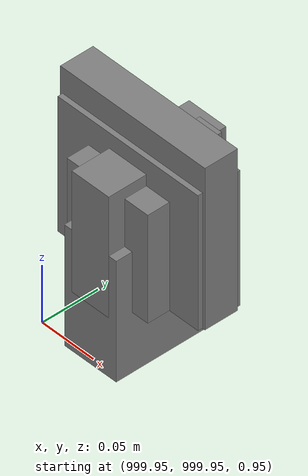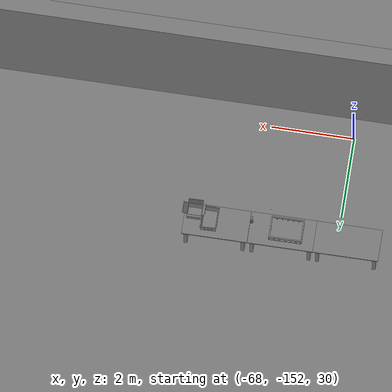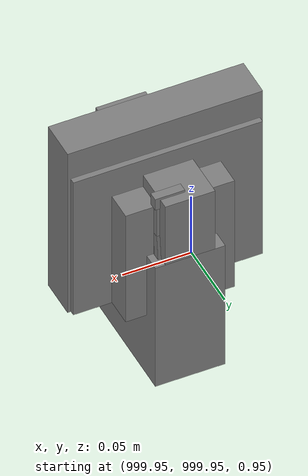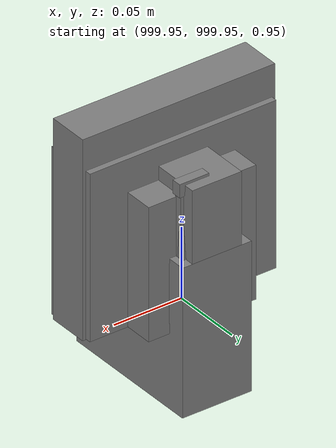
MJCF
<mujoco>
    <option gravity="0.000000000 0.000000000 -9.810000420" timestep="0.0049999999" integrator="implicitfast" density="1.225" viscosity="1.8000001e-05" noslip_iterations="10" iterations="100" sdf_iterations="50">
        <flag multiccd="disable"/>
    </option>
    <size memory="1000M"/>
    <compiler coordinate="local"/>
    <worldbody>
        <light cutoff="30" pos="0 1 1" dir="0 -1 -2"/>
        <light cutoff="30" pos="0 -1 1" dir="0 1 -2"/>
        <body pos="-65.808143616 -149.680526733 31.167057037" euler="-127.517845154 66.954963684 -105.336425781" mocap="true" name="spotlight4_SpotLight"/>
        <body pos="-66.330253601 -149.719421387 31.167270660" euler="-24.723054886 13.359145164 -108.109283447" mocap="true" name="spotlight2_SpotLight"/>
        <body pos="-66.129188538 -149.632263184 31.171485901" euler="139.945968628 42.510425568 -119.710632324" mocap="true" name="spotlight3_SpotLight"/>
        <body pos="1000.000000000 1000.000000000 1.000000000" euler="0.000000000 0.000000000 180.000000000" name="openloong_gripper_2f85_fix_base_usda_cpu_fan">
            <geom contype="1" conaffinity="1" density="1000" type="box" material="" rgba="0.500000000 0.500000000 0.500000000 1.000000000" solimp="0.899999976 0.949999988 0.001000000" friction="1.000000000 0.005000000 0.000100000" solref="0.020000000 1.000000000" margin="0" condim="3" group="0" pos="0.000000000 0.000000000 0.070034981" quat="0.000000000 0.000000000 0.000000000 1.000000000" size="0.070700005 0.014699999 0.070700005" name="openloong_gripper_2f85_fix_base_usda_geom_3FB7FCCD_CADD_45D9_90FF_99899EB79DA8"/>
            <freejoint name="openloong_gripper_2f85_fix_base_usda_cpu_fan_joint"/>
            <site size="0.005000000 0.005000000 0.005000000" rgba="0.500000000 0.500000000 0.500000000 1.000000000" pos="0.000000000 0.000000000 0.000000000" quat="0.999961913 0.008726535 0.000000000 0.000000000" group="0" type="sphere" name="openloong_gripper_2f85_fix_base_usda_cpu_fancsite"/>
        </body>
        <body pos="1000.000000000 999.999938965 1.000000000" euler="0.000000000 0.000000000 180.000000000" name="openloong_gripper_2f85_fix_base_usda_intelcore_i5">
            <geom contype="1" conaffinity="1" density="1000" type="box" material="" rgba="0.500000000 0.500000000 0.500000000 1.000000000" solimp="0.899999976 0.949999988 0.001000000" friction="1.000000000 0.005000000 0.000100000" solref="0.020000000 1.000000000" margin="0" condim="3" group="0" pos="0.000000000 0.000000000 0.051722717" quat="0.707106709 0.000000000 0.000000000 -0.707106769" size="0.052800000 0.018080002 0.052800000" name="openloong_gripper_2f85_fix_base_usda_geom_89EB712F_6085_4920_9C74_08BC004C00DB"/>
            <freejoint name="openloong_gripper_2f85_fix_base_usda_intelcore_i5_joint"/>
            <site size="0.005000000 0.005000000 0.005000000" rgba="0.500000000 0.500000000 0.500000000 1.000000000" pos="0.000000000 0.000000000 0.000000000" quat="0.999961913 0.008726534 0.000000000 0.000000000" group="0" type="sphere" name="openloong_gripper_2f85_fix_base_usda_intelcore_i5site"/>
        </body>
        <body pos="1000.000000000 1000.000000000 1.000000000" euler="0.000000000 0.000000000 180.000000000" name="openloong_gripper_2f85_fix_base_usda_battery_01">
            <geom contype="1" conaffinity="1" density="1000" type="box" material="" rgba="0.500000000 0.500000000 0.500000000 1.000000000" solimp="0.899999976 0.949999988 0.001000000" friction="1.000000000 0.005000000 0.000100000" solref="0.020000000 1.000000000" margin="0" condim="3" group="0" pos="-0.011123657 -0.041940309 0.101691343" quat="1.000000000 0.000000000 0.000000000 0.000000000" size="0.010800000 0.003375000 0.004725000" name="openloong_gripper_2f85_fix_base_usda_geom_27B11486_3E16_4C91_9856_9A88644F8114"/>
            <geom contype="1" conaffinity="1" density="1000" type="box" material="" rgba="0.500000000 0.500000000 0.500000000 1.000000000" solimp="0.899999976 0.949999988 0.001000000" friction="1.000000000 0.005000000 0.000100000" solref="0.020000000 1.000000000" margin="0" condim="3" group="0" pos="-0.010876465 -0.044247437 0.047066893" quat="0.998702705 -0.050920475 0.000000000 0.000000000" size="0.009450001 0.002700000 0.024975000" name="openloong_gripper_2f85_fix_base_usda_geom_6FFF4CD6_9145_4F63_9D6F_5A10CEBBD1CD"/>
            <geom contype="1" conaffinity="1" density="1000" type="box" material="" rgba="0.500000000 0.500000000 0.500000000 1.000000000" solimp="0.899999976 0.949999988 0.001000000" friction="1.000000000 0.005000000 0.000100000" solref="0.020000000 1.000000000" margin="0" condim="3" group="0" pos="-0.001235962 -0.000659180 0.047381196" quat="1.000000000 0.000000000 0.000000000 0.000000000" size="0.039420001 0.039150000 0.047250003" name="openloong_gripper_2f85_fix_base_usda_geom_397E5E82_9B25_4C57_B6A7_7B4F04DF2D1A"/>
            <geom contype="1" conaffinity="1" density="1000" type="box" material="" rgba="0.500000000 0.500000000 0.500000000 1.000000000" solimp="0.899999976 0.949999988 0.001000000" friction="1.000000000 0.005000000 0.000100000" solref="0.020000000 1.000000000" margin="0" condim="3" group="0" pos="-0.010876465 -0.039138794 0.009851727" quat="1.000000000 0.000000000 0.000000000 0.000000000" size="0.009450001 0.010800000 0.013500000" name="openloong_gripper_2f85_fix_base_usda_geom_FDCB2E4B_267E_468E_99E7_1CFB67E77548"/>
            <geom contype="1" conaffinity="1" density="1000" type="box" material="" rgba="0.500000000 0.500000000 0.500000000 1.000000000" solimp="0.899999976 0.949999988 0.001000000" friction="1.000000000 0.005000000 0.000100000" solref="0.020000000 1.000000000" margin="0" condim="3" group="0" pos="-0.010876465 -0.041528322 0.071508206" quat="1.000000000 0.000000000 0.000000000 0.000000000" size="0.009450001 0.002700000 0.027000001" name="openloong_gripper_2f85_fix_base_usda_geom_5F2B8659_FE68_41F8_A3BE_A877E721D887"/>
            <freejoint name="openloong_gripper_2f85_fix_base_usda_battery_01_joint"/>
            <site size="0.005000000 0.005000000 0.005000000" rgba="0.500000000 0.500000000 0.500000000 1.000000000" pos="0.000000000 0.000000000 0.000000000" quat="0.999961913 0.008726500 0.000000000 0.000000000" group="0" type="sphere" name="openloong_gripper_2f85_fix_base_usda_battery_01site"/>
        </body>
        <body pos="1000.000000000 1000.000000000 1.000000000" euler="0.000000000 0.000000000 180.000000000" name="openloong_gripper_2f85_fix_base_usda_wifi_box">
            <geom contype="1" conaffinity="1" density="1000" type="box" material="" rgba="0.500000000 0.500000000 0.500000000 1.000000000" solimp="0.899999976 0.949999988 0.001000000" friction="1.000000000 0.005000000 0.000100000" solref="0.020000000 1.000000000" margin="0" condim="3" group="0" pos="0.000000000 0.000000000 0.058978677" quat="0.000000000 0.000000047 0.000000000 1.000000000" size="0.068499997 0.018999999 0.059000000" name="openloong_gripper_2f85_fix_base_usda_geom_826A5273_FF70_4403_B1AF_BF8C364ED9B7"/>
            <freejoint name="openloong_gripper_2f85_fix_base_usda_wifi_box_joint"/>
            <site size="0.005000000 0.005000000 0.005000000" rgba="0.500000000 0.500000000 0.500000000 1.000000000" pos="0.000000000 0.000000000 0.000000000" quat="0.999961913 0.008726500 0.000000000 0.000000000" group="0" type="sphere" name="openloong_gripper_2f85_fix_base_usda_wifi_boxsite"/>
        </body>
        <body pos="1000.000000000 1000.000000000 1.000000000" euler="0.000011953 0.000005123 -179.999984741" name="openloong_gripper_2f85_fix_base_usda_intel_box">
            <geom contype="1" conaffinity="1" density="1000" type="box" material="" rgba="0.500000000 0.500000000 0.500000000 1.000000000" solimp="0.899999976 0.949999988 0.001000000" friction="1.000000000 0.005000000 0.000100000" solref="0.020000000 1.000000000" margin="0" condim="3" group="0" pos="0.000000000 -0.000067139 0.000082284" quat="0.707106709 0.000000225 0.000000253 0.707106650" size="0.052800003 0.025300000 0.052800003" name="openloong_gripper_2f85_fix_base_usda_geom_966B080F_9DD6_4B81_88A0_B01B70D3E8E7"/>
            <freejoint name="openloong_gripper_2f85_fix_base_usda_intel_box_joint"/>
            <site size="0.005000000 0.005000000 0.005000000" rgba="0.500000000 0.500000000 0.500000000 1.000000000" pos="0.000000000 0.000000000 0.000000000" quat="0.999961913 0.008726500 0.000000000 0.000000000" group="0" type="sphere" name="openloong_gripper_2f85_fix_base_usda_intel_boxsite"/>
        </body>
        <body pos="-64.866622925 -149.383972168 30.183746338" euler="89.999984741 89.999946594 0.000000000" name="openloong_gripper_2f85_fix_base_usda_bluebox_01">
            <geom contype="1" conaffinity="1" density="1000" type="box" material="" rgba="0.500000000 0.500000000 0.500000000 1.000000000" solimp="0.899999976 0.949999988 0.001000000" friction="1.000000000 0.005000000 0.000100000" solref="0.020000000 1.000000000" margin="0" condim="3" group="0" pos="0.276580811 0.187225342 0.000068665" quat="0.707106948 0.000077471 0.707106352 0.000077486" size="0.100000001 0.057999998 0.010000000" name="openloong_gripper_2f85_fix_base_usda_geom_BD0713D7_6333_469E_9222_E7B2706E7290"/>
            <geom contype="1" conaffinity="1" density="1000" type="box" material="" rgba="0.500000000 0.500000000 0.500000000 1.000000000" solimp="0.899999976 0.949999988 0.001000000" friction="1.000000000 0.005000000 0.000100000" solref="0.020000000 1.000000000" margin="0" condim="3" group="0" pos="0.000000000 0.002883911 0.000000000" quat="0.999999881 0.000000000 0.000000000 0.000000000" size="0.254000008 0.003000000 0.172000006" name="openloong_gripper_2f85_fix_base_usda_geom_13F6AE4F_6BA3_449A_8E09_44A4D4AC4364"/>
            <geom contype="1" conaffinity="1" density="1000" type="box" material="" rgba="0.500000000 0.500000000 0.500000000 1.000000000" solimp="0.899999976 0.949999988 0.001000000" friction="1.000000000 0.005000000 0.000100000" solref="0.020000000 1.000000000" margin="0" condim="3" group="0" pos="0.000000000 0.124874115 0.173484802" quat="0.999796331 0.020176515 -0.000000015 0.000000030" size="0.259999990 0.119999997 0.007000000" name="openloong_gripper_2f85_fix_base_usda_geom_5E238886_A02E_41BA_841F_4A0D7B6C6494"/>
            <geom contype="1" conaffinity="1" density="1000" type="box" material="" rgba="0.500000000 0.500000000 0.500000000 1.000000000" solimp="0.899999976 0.949999988 0.001000000" friction="1.000000000 0.005000000 0.000100000" solref="0.020000000 1.000000000" margin="0" condim="3" group="0" pos="0.000000000 0.124874115 -0.173469543" quat="0.999796331 -0.020176545 -0.000000015 0.000000000" size="0.259999990 0.119999997 0.007000000" name="openloong_gripper_2f85_fix_base_usda_geom_7B766D1E_2659_46C6_9AD9_7A392873558F"/>
            <geom contype="1" conaffinity="1" density="1000" type="box" material="" rgba="0.500000000 0.500000000 0.500000000 1.000000000" solimp="0.899999976 0.949999988 0.001000000" friction="1.000000000 0.005000000 0.000100000" solref="0.020000000 1.000000000" margin="0" condim="3" group="0" pos="0.000000000 0.214008331 0.188980103" quat="0.999912977 0.013176724 0.000000015 0.000000000" size="0.259999990 0.029999999 0.012500000" name="openloong_gripper_2f85_fix_base_usda_geom_A8365F4C_8A15_47A0_A840_CDC651D4B614"/>
            <geom contype="1" conaffinity="1" density="1000" type="box" material="" rgba="0.500000000 0.500000000 0.500000000 1.000000000" solimp="0.899999976 0.949999988 0.001000000" friction="1.000000000 0.005000000 0.000100000" solref="0.020000000 1.000000000" margin="0" condim="3" group="0" pos="-0.258361816 0.125289917 0.001876831" quat="0.702796936 -0.020792112 0.710783124 0.020769298" size="0.189999998 0.119999997 0.009000000" name="openloong_gripper_2f85_fix_base_usda_geom_59DC4009_2253_4625_8DE0_506ADBB14081"/>
            <geom contype="1" conaffinity="1" density="1000" type="box" material="" rgba="0.500000000 0.500000000 0.500000000 1.000000000" solimp="0.899999976 0.949999988 0.001000000" friction="1.000000000 0.005000000 0.000100000" solref="0.020000000 1.000000000" margin="0" condim="3" group="0" pos="0.000000000 0.214008331 -0.188980103" quat="0.999912977 -0.013176769 0.000000030 0.000000015" size="0.259999990 0.029999999 0.012500000" name="openloong_gripper_2f85_fix_base_usda_geom_FFE8107D_DF56_409B_B844_3A2DB27ED908"/>
            <geom contype="1" conaffinity="1" density="1000" type="box" material="" rgba="0.500000000 0.500000000 0.500000000 1.000000000" solimp="0.899999976 0.949999988 0.001000000" friction="1.000000000 0.005000000 0.000100000" solref="0.020000000 1.000000000" margin="0" condim="3" group="0" pos="-0.276611328 0.187225342 0.000068665" quat="0.707106650 0.000077441 0.707106709 0.000077456" size="0.100000001 0.057999998 0.010000000" name="openloong_gripper_2f85_fix_base_usda_geom_189F9C4C_05B2_4C24_BD97_C400736BFD34"/>
            <geom contype="1" conaffinity="1" density="1000" type="box" material="" rgba="0.500000000 0.500000000 0.500000000 1.000000000" solimp="0.899999976 0.949999988 0.001000000" friction="1.000000000 0.005000000 0.000100000" solref="0.020000000 1.000000000" margin="0" condim="3" group="0" pos="0.258331299 0.125289917 0.001876831" quat="0.702851415 0.018856421 0.710823774 -0.019329369" size="0.189999998 0.119999997 0.009000000" name="openloong_gripper_2f85_fix_base_usda_geom_8F04320E_FB74_4876_8155_64B53E564E4C"/>
            <freejoint name="openloong_gripper_2f85_fix_base_usda_bluebox_01_joint"/>
            <site size="0.005000000 0.005000000 0.005000000" rgba="0.500000000 0.500000000 0.500000000 1.000000000" pos="0.000000000 0.000000000 0.000000000" quat="0.999961913 0.008726534 0.000000000 0.000000000" group="0" type="sphere" name="openloong_gripper_2f85_fix_base_usda_bluebox_01site"/>
        </body>
        <body pos="-64.496299744 -149.491867065 30.235729218" euler="0.000000000 0.000000000 89.999946594" name="openloong_gripper_2f85_fix_base_usda_cardboardbox_01">
            <geom contype="1" conaffinity="1" density="1000" type="box" material="" rgba="0.500000000 0.500000000 0.500000000 1.000000000" solimp="0.899999976 0.949999988 0.001000000" friction="1.000000000 0.005000000 0.000100000" solref="0.020000000 1.000000000" margin="0" condim="3" group="0" pos="-0.003166199 -0.004086494 0.005052090" quat="1.000000000 0.000000000 0.000000000 0.000000000" size="0.142499998 0.177500010 0.005000000" name="openloong_gripper_2f85_fix_base_usda_geom_5E3740D1_F9C0_429F_95F2_303B26CA17BB"/>
            <geom contype="1" conaffinity="1" density="1000" type="box" material="" rgba="0.500000000 0.500000000 0.500000000 1.000000000" solimp="0.899999976 0.949999988 0.001000000" friction="1.000000000 0.005000000 0.000100000" solref="0.020000000 1.000000000" margin="0" condim="3" group="0" pos="-0.003166199 0.170316696 0.150570869" quat="1.000000000 0.000000000 0.000000000 0.000000000" size="0.142499998 0.005000000 0.149999991" name="openloong_gripper_2f85_fix_base_usda_geom_AE12A472_90CF_4D7F_B801_FAFE06678FEF"/>
            <geom contype="1" conaffinity="1" density="1000" type="box" material="" rgba="0.500000000 0.500000000 0.500000000 1.000000000" solimp="0.899999976 0.949999988 0.001000000" friction="1.000000000 0.005000000 0.000100000" solref="0.020000000 1.000000000" margin="0" condim="3" group="0" pos="-0.147399902 -0.005307198 0.150570869" quat="1.000000000 0.000000000 0.000000000 0.000000000" size="0.005000000 0.177500010 0.149999991" name="openloong_gripper_2f85_fix_base_usda_geom_BF28B488_EC45_47FC_9184_F6B0EBA33F32"/>
            <geom contype="1" conaffinity="1" density="1000" type="box" material="" rgba="0.500000000 0.500000000 0.500000000 1.000000000" solimp="0.899999976 0.949999988 0.001000000" friction="1.000000000 0.005000000 0.000100000" solref="0.020000000 1.000000000" margin="0" condim="3" group="0" pos="0.140275955 -0.005307198 0.150570869" quat="1.000000000 0.000000000 0.000000000 0.000000000" size="0.005000000 0.177500010 0.149999991" name="openloong_gripper_2f85_fix_base_usda_geom_A4EA36D0_56EE_42CA_9FFC_AE77D0E14E1A"/>
            <geom contype="1" conaffinity="1" density="1000" type="box" material="" rgba="0.500000000 0.500000000 0.500000000 1.000000000" solimp="0.899999976 0.949999988 0.001000000" friction="1.000000000 0.005000000 0.000100000" solref="0.020000000 1.000000000" margin="0" condim="3" group="0" pos="-0.003166199 -0.181550980 0.150570869" quat="1.000000000 0.000000000 0.000000000 0.000000000" size="0.142499998 0.005000000 0.149999991" name="openloong_gripper_2f85_fix_base_usda_geom_FE3C42A7_1BF6_4A91_A917_38F4DA291A83"/>
            <freejoint name="openloong_gripper_2f85_fix_base_usda_cardboardbox_01_joint"/>
            <site size="0.005000000 0.005000000 0.005000000" rgba="0.500000000 0.500000000 0.500000000 1.000000000" pos="0.000000000 0.000000000 0.000000000" quat="0.999961913 0.008726535 0.000000000 0.000000000" group="0" type="sphere" name="openloong_gripper_2f85_fix_base_usda_site_297B4026_E3EA_472F_8389_BB445EC967FC"/>
            <body pos="0.139160156 -0.004048347 0.301930904" euler="-179.999954224 49.383502960 179.999954224" name="openloong_gripper_2f85_fix_base_usda_A1_006">
                <geom contype="1" conaffinity="1" density="1000" type="box" material="" rgba="0.500000000 0.500000000 0.500000000 1.000000000" solimp="0.899999976 0.949999988 0.001000000" friction="1.000000000 0.005000000 0.000100000" solref="0.020000000 1.000000000" margin="0" condim="3" group="0" pos="-0.071587563 0.000009537 0.001745224" quat="0.999999881 0.000000000 0.000000000 0.000000000" size="0.071249999 0.179999992 0.002500000" name="openloong_gripper_2f85_fix_base_usda_geom_F119968E_E613_41CF_B327_2062BD1E9B72"/>
                <joint armature="0" stiffness="0.07" damping="0.0099999998" axis="0.000000 1.000000 0.000000" type="hinge" name="openloong_gripper_2f85_fix_base_usda_A1_006"/>
            </body>
            <body pos="-0.145902634 -0.004086494 0.301938057" euler="-180.000000000 -60.000011444 -180.000000000" name="openloong_gripper_2f85_fix_base_usda_A2_006">
                <geom contype="1" conaffinity="1" density="1000" type="box" material="" rgba="0.500000000 0.500000000 0.500000000 1.000000000" solimp="0.899999976 0.949999988 0.001000000" friction="1.000000000 0.005000000 0.000100000" solref="0.020000000 1.000000000" margin="0" condim="3" group="0" pos="0.071268082 0.000009537 0.002717972" quat="0.000002921 0.000000000 -0.000000030 0.999999881" size="0.071249999 0.179999992 0.002500000" name="openloong_gripper_2f85_fix_base_usda_geom_1E55C4B0_943B_4628_86A6_4142A01B902C"/>
                <joint armature="0" stiffness="0.07" damping="0.0099999998" axis="0.000000 1.000000 0.000000" type="hinge" name="openloong_gripper_2f85_fix_base_usda_A2_006"/>
            </body>
            <body pos="-0.003385544 0.175991058 0.301930904" euler="-125.858116150 -0.000004561 0.000002331" name="openloong_gripper_2f85_fix_base_usda_B2_006">
                <geom contype="1" conaffinity="1" density="1000" type="box" material="" rgba="0.500000000 0.500000000 0.500000000 1.000000000" solimp="0.899999976 0.949999988 0.001000000" friction="1.000000000 0.005000000 0.000100000" solref="0.020000000 1.000000000" margin="0" condim="3" group="0" pos="0.000009537 -0.070939064 -0.002470016" quat="0.999614120 0.027776197 -0.000000015 0.000000030" size="0.137500003 0.064999998 0.005000000" name="openloong_gripper_2f85_fix_base_usda_geom_EBE75015_87BF_40CF_8AE3_EF7F2F9A1EE1"/>
                <joint armature="0" stiffness="0.07" damping="0.0099999998" axis="1.000000 0.000000 0.000000" type="hinge" name="openloong_gripper_2f85_fix_base_usda_B2_006"/>
            </body>
            <body pos="-0.003385544 -0.184140205 0.301938057" euler="147.805557251 0.000000000 0.000000000" name="openloong_gripper_2f85_fix_base_usda_B1_006">
                <geom contype="1" conaffinity="1" density="1000" type="box" material="" rgba="0.500000000 0.500000000 0.500000000 1.000000000" solimp="0.899999976 0.949999988 0.001000000" friction="1.000000000 0.005000000 0.000100000" solref="0.020000000 1.000000000" margin="0" condim="3" group="0" pos="-0.000028610 0.070202351 -0.002703667" quat="0.999614179 -0.027776167 0.000000000 0.000000000" size="0.137500003 0.064999998 0.005000000" name="openloong_gripper_2f85_fix_base_usda_geom_F12499CA_EE08_4F5C_B7C2_4F29875DCAB1"/>
                <joint armature="0" stiffness="0.07" damping="0.0099999998" axis="1.000000 0.000000 0.000000" type="hinge" name="openloong_gripper_2f85_fix_base_usda_B1_006"/>
            </body>
        </body>
        <body pos="-65.882858276 -149.481979370 30.229999542" euler="-64.487716675 0.000000000 0.000000000" name="openloong_gripper_2f85_fix_base_usda_Barcode">
            <geom contype="1" conaffinity="1" density="1000" type="box" material="" rgba="0.500000000 0.500000000 0.500000000 1.000000000" solimp="0.899999976 0.949999988 0.001000000" friction="1.000000000 0.005000000 0.000100000" solref="0.020000000 1.000000000" margin="0" condim="3" group="0" pos="0.000000000 0.013038635 0.001419067" quat="0.000000000 0.000000000 0.000000000 1.000000119" size="0.034000002 0.010000000 0.017999999" name="openloong_gripper_2f85_fix_base_usda_geom_DE969DE9_3CEB_470C_BDD9_1DFF4B5E6FCD"/>
            <geom contype="1" conaffinity="1" density="1000" type="box" material="" rgba="0.500000000 0.500000000 0.500000000 1.000000000" solimp="0.899999976 0.949999988 0.001000000" friction="1.000000000 0.005000000 0.000100000" solref="0.020000000 1.000000000" margin="0" condim="3" group="0" pos="0.000000000 -0.035301208 -0.007095337" quat="0.000000000 0.000000000 -0.043619365 0.999048233" size="0.028999999 0.010000000 0.020000000" name="openloong_gripper_2f85_fix_base_usda_geom_4FCEE3F0_A234_4451_8350_4EBC867C446E"/>
            <geom contype="1" conaffinity="1" density="1000" type="box" material="" rgba="0.500000000 0.500000000 0.500000000 1.000000000" solimp="0.899999976 0.949999988 0.001000000" friction="1.000000000 0.005000000 0.000100000" solref="0.020000000 1.000000000" margin="0" condim="3" group="0" pos="0.000000000 -0.043411255 -0.011749268" quat="0.922262907 0.386563420 0.000000000 0.000000000" size="0.026000001 0.010000000 0.020000000" name="openloong_gripper_2f85_fix_base_usda_geom_A5EF60CD_309A_42AA_BA0A_35B053396C36"/>
            <geom contype="1" conaffinity="1" density="1000" type="box" material="" rgba="0.500000000 0.500000000 0.500000000 1.000000000" solimp="0.899999976 0.949999988 0.001000000" friction="1.000000000 0.005000000 0.000100000" solref="0.020000000 1.000000000" margin="0" condim="3" group="0" pos="0.000000000 -0.016967773 -0.031860352" quat="0.000000000 0.000000000 0.000000000 1.000000119" size="0.008000000 0.010000000 0.013000000" name="openloong_gripper_2f85_fix_base_usda_geom_B3DB1F98_7FD6_4EF0_8C6F_DDB318533AAC"/>
            <geom contype="1" conaffinity="1" density="1000" type="box" material="" rgba="0.500000000 0.500000000 0.500000000 1.000000000" solimp="0.899999976 0.949999988 0.001000000" friction="1.000000000 0.005000000 0.000100000" solref="0.020000000 1.000000000" margin="0" condim="3" group="0" pos="0.000000000 -0.001869202 0.000312805" quat="0.953716993 0.300705761 0.000000000 0.000000000" size="0.032000002 0.010000000 0.018999999" name="openloong_gripper_2f85_fix_base_usda_geom_52997C70_9D79_465D_8B3F_9EAE748253E0"/>
            <geom contype="1" conaffinity="1" density="1000" type="box" material="" rgba="0.500000000 0.500000000 0.500000000 1.000000000" solimp="0.899999976 0.949999988 0.001000000" friction="1.000000000 0.005000000 0.000100000" solref="0.020000000 1.000000000" margin="0" condim="3" group="0" pos="0.000000000 -0.019531250 -0.003173828" quat="0.953716993 0.300705761 0.000000000 0.000000000" size="0.030999999 0.010000000 0.020000000" name="openloong_gripper_2f85_fix_base_usda_geom_C5CFCC80_70DA_47FD_8A7C_DBBC20628A46"/>
            <geom contype="1" conaffinity="1" density="1000" type="box" material="" rgba="0.500000000 0.500000000 0.500000000 1.000000000" solimp="0.899999976 0.949999988 0.001000000" friction="1.000000000 0.005000000 0.000100000" solref="0.020000000 1.000000000" margin="0" condim="3" group="0" pos="0.000000000 -0.035301208 -0.007095337" quat="0.953716993 0.300705761 0.000000000 0.000000000" size="0.028999999 0.010000000 0.020000000" name="openloong_gripper_2f85_fix_base_usda_geom_B7316E2B_3233_41CE_87D3_CCC52FE14FC1"/>
            <geom contype="1" conaffinity="1" density="1000" type="box" material="" rgba="0.500000000 0.500000000 0.500000000 1.000000000" solimp="0.899999976 0.949999988 0.001000000" friction="1.000000000 0.005000000 0.000100000" solref="0.020000000 1.000000000" margin="0" condim="3" group="0" pos="0.000000000 -0.042617798 -0.071121216" quat="0.000000000 0.000000000 0.000000000 1.000000119" size="0.013000000 0.021000000 0.059999999" name="openloong_gripper_2f85_fix_base_usda_geom_7E9A36C2_54D5_4678_9A9E_08E9DB798745"/>
            <freejoint name="openloong_gripper_2f85_fix_base_usda_Barcode_joint"/>
            <site size="0.005000000 0.005000000 0.005000000" rgba="0.500000000 0.500000000 0.500000000 1.000000000" pos="0.000000000 0.000000000 0.000000000" quat="1.000000000 0.000000000 0.000000000 0.000000000" group="0" type="sphere" name="openloong_gripper_2f85_fix_base_usda_Barcode_site"/>
        </body>
        <body pos="-66.745018005 -149.392349243 30.184000015" euler="0.000000000 0.000000000 89.999946594" name="[22330048461272]_Basket_01">
            <geom contype="1" conaffinity="1" density="1000" type="box" material="" rgba="0.500000000 0.500000000 0.500000000 1.000000000" solimp="0.899999976 0.949999988 0.001000000" friction="1.000000000 0.005000000 0.000100000" solref="0.020000000 1.000000000" margin="0" condim="3" group="0" pos="-0.052425385 0.389207840 0.089787483" quat="0.707107008 0.000000000 0.000000000 0.707106411" size="0.014249999 0.014249999 0.059999999" name="[22330048461272]_geom_0C696857_8512_43C8_B8E0_89AC58DA03D9"/>
            <geom contype="1" conaffinity="1" density="1000" type="box" material="" rgba="0.500000000 0.500000000 0.500000000 1.000000000" solimp="0.899999976 0.949999988 0.001000000" friction="1.000000000 0.005000000 0.000100000" solref="0.020000000 1.000000000" margin="0" condim="3" group="0" pos="0.264015198 -0.133043289 0.089787483" quat="0.707107008 0.000000000 0.000000000 0.707106411" size="0.014249999 0.014249999 0.059999999" name="[22330048461272]_geom_A77102D8_EAA5_44AE_BB50_A2A399905B31"/>
            <geom contype="1" conaffinity="1" density="1000" type="box" material="" rgba="0.500000000 0.500000000 0.500000000 1.000000000" solimp="0.899999976 0.949999988 0.001000000" friction="1.000000000 0.005000000 0.000100000" solref="0.020000000 1.000000000" margin="0" condim="3" group="0" pos="-0.264015198 -0.265548706 0.089793205" quat="0.707107008 0.000000000 0.000000000 0.707106411" size="0.014249999 0.014249999 0.059999999" name="[22330048461272]_geom_830926FC_D7A4_45CD_B062_04941F25097E"/>
            <geom contype="1" conaffinity="1" density="1000" type="box" material="" rgba="0.500000000 0.500000000 0.500000000 1.000000000" solimp="0.899999976 0.949999988 0.001000000" friction="1.000000000 0.005000000 0.000100000" solref="0.020000000 1.000000000" margin="0" condim="3" group="0" pos="-0.160263062 -0.389322281 0.089793205" quat="0.707107008 0.000000000 0.000000000 0.707106411" size="0.014249999 0.014249999 0.059999999" name="[22330048461272]_geom_F1F84B3D_2145_46D8_982C_01EC81B73898"/>
            <geom contype="1" conaffinity="1" density="1000" type="box" material="" rgba="0.500000000 0.500000000 0.500000000 1.000000000" solimp="0.899999976 0.949999988 0.001000000" friction="1.000000000 0.005000000 0.000100000" solref="0.020000000 1.000000000" margin="0" condim="3" group="0" pos="0.162265778 -0.389322281 0.089787483" quat="0.707107008 0.000000000 0.000000000 0.707106411" size="0.014249999 0.014249999 0.059999999" name="[22330048461272]_geom_F434C151_5D91_4F67_904B_6EE4705B4DB7"/>
            <geom contype="1" conaffinity="1" density="1000" type="box" material="" rgba="0.500000000 0.500000000 0.500000000 1.000000000" solimp="0.899999976 0.949999988 0.001000000" friction="1.000000000 0.005000000 0.000100000" solref="0.020000000 1.000000000" margin="0" condim="3" group="0" pos="0.264015198 0.389207840 0.089787483" quat="0.707107008 0.000000000 0.000000000 0.707106411" size="0.014249999 0.014249999 0.059999999" name="[22330048461272]_geom_C157906B_B261_4A6C_9C64_023535D1D2CF"/>
            <geom contype="1" conaffinity="1" density="1000" type="box" material="" rgba="0.500000000 0.500000000 0.500000000 1.000000000" solimp="0.899999976 0.949999988 0.001000000" friction="1.000000000 0.005000000 0.000100000" solref="0.020000000 1.000000000" margin="0" condim="3" group="0" pos="-0.264015198 -0.133043289 0.089793205" quat="0.707107008 0.000000000 0.000000000 0.707106411" size="0.014249999 0.014249999 0.059999999" name="[22330048461272]_geom_BE1352DA_585D_4C84_8596_29F9CE6A1D1C"/>
            <geom contype="1" conaffinity="1" density="1000" type="box" material="" rgba="0.500000000 0.500000000 0.500000000 1.000000000" solimp="0.899999976 0.949999988 0.001000000" friction="1.000000000 0.005000000 0.000100000" solref="0.020000000 1.000000000" margin="0" condim="3" group="0" pos="-0.264026642 0.269256592 0.089793205" quat="0.707107008 0.000000000 0.000000000 0.707106411" size="0.014249999 0.014249999 0.059999999" name="[22330048461272]_geom_05347284_4C2E_41FF_977C_36BC736790E4"/>
            <geom contype="1" conaffinity="1" density="1000" type="box" material="" rgba="0.500000000 0.500000000 0.500000000 1.000000000" solimp="0.899999976 0.949999988 0.001000000" friction="1.000000000 0.005000000 0.000100000" solref="0.020000000 1.000000000" margin="0" condim="3" group="0" pos="0.054462433 0.389207840 0.089787483" quat="0.707107008 0.000000000 0.000000000 0.707106411" size="0.014249999 0.014249999 0.059999999" name="[22330048461272]_geom_9973C0D4_BA03_4607_ADD6_DF6239822C5E"/>
            <geom contype="1" conaffinity="1" density="1000" type="box" material="" rgba="0.500000000 0.500000000 0.500000000 1.000000000" solimp="0.899999976 0.949999988 0.001000000" friction="1.000000000 0.005000000 0.000100000" solref="0.020000000 1.000000000" margin="0" condim="3" group="0" pos="0.054462433 -0.389322281 0.089787483" quat="0.707107008 0.000000000 0.000000000 0.707106411" size="0.014249999 0.014249999 0.059999999" name="[22330048461272]_geom_F4C08881_357F_47AA_B091_AFBC2E57C612"/>
            <geom contype="1" conaffinity="1" density="1000" type="box" material="" rgba="0.500000000 0.500000000 0.500000000 1.000000000" solimp="0.899999976 0.949999988 0.001000000" friction="1.000000000 0.005000000 0.000100000" solref="0.020000000 1.000000000" margin="0" condim="3" group="0" pos="0.264015198 0.269256592 0.089793205" quat="0.707107008 0.000000000 0.000000000 0.707106411" size="0.014249999 0.014249999 0.059999999" name="[22330048461272]_geom_B1DA274F_D6ED_44FB_A5BD_A67F63522558"/>
            <geom contype="1" conaffinity="1" density="1000" type="box" material="" rgba="0.500000000 0.500000000 0.500000000 1.000000000" solimp="0.899999976 0.949999988 0.001000000" friction="1.000000000 0.005000000 0.000100000" solref="0.020000000 1.000000000" margin="0" condim="3" group="0" pos="0.264015198 -0.389322281 0.089787483" quat="0.707107008 0.000000000 0.000000000 0.707106411" size="0.014249999 0.014249999 0.059999999" name="[22330048461272]_geom_BA86819A_42E2_4E9E_A5D7_5957976A6653"/>
            <geom contype="1" conaffinity="1" density="1000" type="box" material="" rgba="0.500000000 0.500000000 0.500000000 1.000000000" solimp="0.899999976 0.949999988 0.001000000" friction="1.000000000 0.005000000 0.000100000" solref="0.020000000 1.000000000" margin="0" condim="3" group="0" pos="0.000000000 0.000000000 0.015998840" quat="0.707107008 0.000000000 0.000000000 0.707106411" size="0.403499991 0.279000014 0.015750000" name="[22330048461272]_geom_89B948A3_7DD5_4FBD_8856_377953B39844"/>
            <geom contype="1" conaffinity="1" density="1000" type="box" material="" rgba="0.500000000 0.500000000 0.500000000 1.000000000" solimp="0.899999976 0.949999988 0.001000000" friction="1.000000000 0.005000000 0.000100000" solref="0.020000000 1.000000000" margin="0" condim="3" group="0" pos="0.000000000 -0.389476776 0.163619041" quat="0.707107008 0.000000000 0.000000000 0.707106411" size="0.015000000 0.277500004 0.015750000" name="[22330048461272]_geom_01851185_6D5C_4BB7_81FE_AF1DDD3E3B3E"/>
            <geom contype="1" conaffinity="1" density="1000" type="box" material="" rgba="0.500000000 0.500000000 0.500000000 1.000000000" solimp="0.899999976 0.949999988 0.001000000" friction="1.000000000 0.005000000 0.000100000" solref="0.020000000 1.000000000" margin="0" condim="3" group="0" pos="0.162265778 0.389207840 0.089787483" quat="0.707107008 0.000000000 0.000000000 0.707106411" size="0.014249999 0.014249999 0.059999999" name="[22330048461272]_geom_2D1B56CD_6BFE_4DBE_B989_E2807B8031C3"/>
            <geom contype="1" conaffinity="1" density="1000" type="box" material="" rgba="0.500000000 0.500000000 0.500000000 1.000000000" solimp="0.899999976 0.949999988 0.001000000" friction="1.000000000 0.005000000 0.000100000" solref="0.020000000 1.000000000" margin="0" condim="3" group="0" pos="0.000000000 0.389471054 0.163619041" quat="0.707107008 0.000000000 0.000000000 0.707106411" size="0.015000000 0.277500004 0.015750000" name="[22330048461272]_geom_1E1C2829_065A_458A_B42B_CED5EAD44E16"/>
            <geom contype="1" conaffinity="1" density="1000" type="box" material="" rgba="0.500000000 0.500000000 0.500000000 1.000000000" solimp="0.899999976 0.949999988 0.001000000" friction="1.000000000 0.005000000 0.000100000" solref="0.020000000 1.000000000" margin="0" condim="3" group="0" pos="-0.263511658 0.000000000 0.163619041" quat="0.707107008 0.000000000 0.000000000 0.707106411" size="0.403499991 0.015000000 0.015750000" name="[22330048461272]_geom_0572FD07_B98C_45DF_9CD0_1A95465BE8DC"/>
            <geom contype="1" conaffinity="1" density="1000" type="box" material="" rgba="0.500000000 0.500000000 0.500000000 1.000000000" solimp="0.899999976 0.949999988 0.001000000" friction="1.000000000 0.005000000 0.000100000" solref="0.020000000 1.000000000" margin="0" condim="3" group="0" pos="-0.264015198 0.141334534 0.089793205" quat="0.707107008 0.000000000 0.000000000 0.707106411" size="0.014249999 0.014249999 0.059999999" name="[22330048461272]_geom_0016DA48_109D_4F1B_B716_4BB41ED2C009"/>
            <geom contype="1" conaffinity="1" density="1000" type="box" material="" rgba="0.500000000 0.500000000 0.500000000 1.000000000" solimp="0.899999976 0.949999988 0.001000000" friction="1.000000000 0.005000000 0.000100000" solref="0.020000000 1.000000000" margin="0" condim="3" group="0" pos="0.264015198 -0.265548706 0.089787483" quat="0.707107008 0.000000000 0.000000000 0.707106411" size="0.014249999 0.014249999 0.059999999" name="[22330048461272]_geom_40C25040_6DA3_4CE5_B789_93C9F9372E9C"/>
            <geom contype="1" conaffinity="1" density="1000" type="box" material="" rgba="0.500000000 0.500000000 0.500000000 1.000000000" solimp="0.899999976 0.949999988 0.001000000" friction="1.000000000 0.005000000 0.000100000" solref="0.020000000 1.000000000" margin="0" condim="3" group="0" pos="-0.160263062 0.389207840 0.089787483" quat="0.707107008 0.000000000 0.000000000 0.707106411" size="0.014249999 0.014249999 0.059999999" name="[22330048461272]_geom_3A80E330_12F8_418A_8296_45A6AC630962"/>
            <geom contype="1" conaffinity="1" density="1000" type="box" material="" rgba="0.500000000 0.500000000 0.500000000 1.000000000" solimp="0.899999976 0.949999988 0.001000000" friction="1.000000000 0.005000000 0.000100000" solref="0.020000000 1.000000000" margin="0" condim="3" group="0" pos="-0.052425385 -0.389322281 0.089787483" quat="0.707107008 0.000000000 0.000000000 0.707106411" size="0.014249999 0.014249999 0.059999999" name="[22330048461272]_geom_408A96D7_69D2_4EDF_AE79_7EAA6CB4C57D"/>
            <geom contype="1" conaffinity="1" density="1000" type="box" material="" rgba="0.500000000 0.500000000 0.500000000 1.000000000" solimp="0.899999976 0.949999988 0.001000000" friction="1.000000000 0.005000000 0.000100000" solref="0.020000000 1.000000000" margin="0" condim="3" group="0" pos="-0.264026642 -0.389322281 0.089793205" quat="0.707107008 0.000000000 0.000000000 0.707106411" size="0.014249999 0.014249999 0.059999999" name="[22330048461272]_geom_84AA3236_C80A_41C4_A27E_72B77CD749CC"/>
            <geom contype="1" conaffinity="1" density="1000" type="box" material="" rgba="0.500000000 0.500000000 0.500000000 1.000000000" solimp="0.899999976 0.949999988 0.001000000" friction="1.000000000 0.005000000 0.000100000" solref="0.020000000 1.000000000" margin="0" condim="3" group="0" pos="0.264015198 0.141334534 0.089787483" quat="0.707107008 0.000000000 0.000000000 0.707106411" size="0.014249999 0.014249999 0.059999999" name="[22330048461272]_geom_A49A3748_3091_47D0_92F6_DD21EAAE66C8"/>
            <geom contype="1" conaffinity="1" density="1000" type="box" material="" rgba="0.500000000 0.500000000 0.500000000 1.000000000" solimp="0.899999976 0.949999988 0.001000000" friction="1.000000000 0.005000000 0.000100000" solref="0.020000000 1.000000000" margin="0" condim="3" group="0" pos="-0.264015198 0.389207840 0.089793205" quat="0.707107008 0.000000000 0.000000000 0.707106411" size="0.014249999 0.014249999 0.059999999" name="[22330048461272]_geom_882F86FB_D1B2_4369_898C_1E2648526002"/>
            <geom contype="1" conaffinity="1" density="1000" type="box" material="" rgba="0.500000000 0.500000000 0.500000000 1.000000000" solimp="0.899999976 0.949999988 0.001000000" friction="1.000000000 0.005000000 0.000100000" solref="0.020000000 1.000000000" margin="0" condim="3" group="0" pos="0.264015198 0.004480362 0.089787483" quat="0.707107008 0.000000000 0.000000000 0.707106411" size="0.014249999 0.014249999 0.059999999" name="[22330048461272]_geom_E74B33EE_A595_4464_AB61_711EFC95BB57"/>
            <geom contype="1" conaffinity="1" density="1000" type="box" material="" rgba="0.500000000 0.500000000 0.500000000 1.000000000" solimp="0.899999976 0.949999988 0.001000000" friction="1.000000000 0.005000000 0.000100000" solref="0.020000000 1.000000000" margin="0" condim="3" group="0" pos="0.263694763 -0.000011444 0.163619041" quat="0.707107008 0.000000000 0.000000000 0.707106411" size="0.403499991 0.015000000 0.015750000" name="[22330048461272]_geom_9D526882_D661_47DF_84F1_8589111642B2"/>
            <geom contype="1" conaffinity="1" density="1000" type="box" material="" rgba="0.500000000 0.500000000 0.500000000 1.000000000" solimp="0.899999976 0.949999988 0.001000000" friction="1.000000000 0.005000000 0.000100000" solref="0.020000000 1.000000000" margin="0" condim="3" group="0" pos="-0.264015198 0.004480362 0.089793205" quat="0.707107008 0.000000000 0.000000000 0.707106411" size="0.014249999 0.014249999 0.059999999" name="[22330048461272]_geom_EF955D74_C1D2_4C57_B34C_44BD2F9BB3F0"/>
            <freejoint name="[22330048461272]_joint_BFB233E4_5C2E_4A5C_B5EF_145F8F7003DD"/>
        </body>
        <body pos="0.000000000 0.000000000 0.000000000" euler="0.000000000 0.000000000 0.000000000" name="Static Objects_Static Objects">
            <geom contype="1" conaffinity="1" density="1000" type="box" material="" rgba="0.500000000 0.500000000 0.500000000 1.000000000" solimp="0.899999976 0.949999988 0.001000000" friction="1.000000000 0.005000000 0.000100000" solref="0.020000000 1.000000000" margin="0" condim="3" group="0" pos="-67.544113159 -149.365814209 29.727830887" quat="0.500000417 0.499999970 0.499999553 0.499999970" size="0.381000012 0.319999993 0.041000001" name="Static Objects_geom_DAB49FD9_DFE0_4318_B606_97F7B8712ECA"/>
            <geom contype="1" conaffinity="1" density="1000" type="box" material="" rgba="0.500000000 0.500000000 0.500000000 1.000000000" solimp="0.899999976 0.949999988 0.001000000" friction="1.000000000 0.005000000 0.000100000" solref="0.020000000 1.000000000" margin="0" condim="3" group="0" pos="-68.239501953 -149.365814209 30.086868286" quat="0.500000417 0.499999970 0.499999553 0.499999970" size="0.370999992 0.039500002 0.745000005" name="Static Objects_geom_03FFB848_94B8_492C_A1C9_4350A122D0E4"/>
            <geom contype="1" conaffinity="1" density="1000" type="box" material="" rgba="0.500000000 0.500000000 0.500000000 1.000000000" solimp="0.899999976 0.949999988 0.001000000" friction="1.000000000 0.005000000 0.000100000" solref="0.020000000 1.000000000" margin="0" condim="3" group="0" pos="-68.239501953 -149.365814209 30.147235870" quat="0.500000417 0.499999970 0.499999553 0.499999970" size="0.400000006 0.022000000 0.800000012" name="Static Objects_geom_0B1FA8C0_1CC2_4501_B66C_354F1934AD22"/>
            <geom contype="1" conaffinity="1" density="1000" type="box" material="" rgba="0.500000000 0.500000000 0.500000000 1.000000000" solimp="0.899999976 0.949999988 0.001000000" friction="1.000000000 0.005000000 0.000100000" solref="0.020000000 1.000000000" margin="0" condim="3" group="0" pos="-68.934890747 -149.365814209 29.727830887" quat="0.500000417 0.499999970 0.499999553 0.499999970" size="0.381000012 0.319999993 0.041000001" name="Static Objects_geom_F0ED210B_FB97_4F57_85A3_0E5F65032562"/>
            <geom contype="1" conaffinity="1" density="1000" type="box" material="" rgba="0.500000000 0.500000000 0.500000000 1.000000000" solimp="0.899999976 0.949999988 0.001000000" friction="1.000000000 0.005000000 0.000100000" solref="0.020000000 1.000000000" margin="0" condim="3" group="0" pos="-68.239501953 -149.365814209 29.561563492" quat="0.500000417 0.499999970 0.499999553 0.499999970" size="0.020000000 0.022000000 0.660000026" name="Static Objects_geom_372737E0_79DB_4C10_A0A7_3A0EA50D1609"/>
            <geom contype="1" conaffinity="1" density="1000" type="box" material="" rgba="0.500000000 0.500000000 0.500000000 1.000000000" solimp="0.899999976 0.949999988 0.001000000" friction="1.000000000 0.005000000 0.000100000" solref="0.020000000 1.000000000" margin="0" condim="3" group="0" pos="-65.945671082 -149.365814209 29.727830887" quat="0.500000417 0.499999970 0.499999553 0.499999970" size="0.381000012 0.319999993 0.041000001" name="Static Objects_geom_08FB3AF7_4A18_44E9_A7A3_A300EF627980"/>
            <geom contype="1" conaffinity="1" density="1000" type="box" material="" rgba="0.500000000 0.500000000 0.500000000 1.000000000" solimp="0.899999976 0.949999988 0.001000000" friction="1.000000000 0.005000000 0.000100000" solref="0.020000000 1.000000000" margin="0" condim="3" group="0" pos="-66.641059875 -149.365814209 30.086868286" quat="0.500000417 0.499999970 0.499999553 0.499999970" size="0.370999992 0.039500002 0.745000005" name="Static Objects_geom_A158F35F_02A2_4F62_AAA8_7AF381DB9F1B"/>
            <geom contype="1" conaffinity="1" density="1000" type="box" material="" rgba="0.500000000 0.500000000 0.500000000 1.000000000" solimp="0.899999976 0.949999988 0.001000000" friction="1.000000000 0.005000000 0.000100000" solref="0.020000000 1.000000000" margin="0" condim="3" group="0" pos="-66.641059875 -149.365814209 30.147235870" quat="0.500000417 0.499999970 0.499999553 0.499999970" size="0.400000006 0.022000000 0.800000012" name="Static Objects_geom_FBB74802_DA30_40B5_9361_089E5079496D"/>
            <geom contype="1" conaffinity="1" density="1000" type="box" material="" rgba="0.500000000 0.500000000 0.500000000 1.000000000" solimp="0.899999976 0.949999988 0.001000000" friction="1.000000000 0.005000000 0.000100000" solref="0.020000000 1.000000000" margin="0" condim="3" group="0" pos="-67.336448669 -149.365814209 29.727830887" quat="0.500000417 0.499999970 0.499999553 0.499999970" size="0.381000012 0.319999993 0.041000001" name="Static Objects_geom_EAB88D1B_11E3_4811_8A97_E1A42E0B43BF"/>
            <geom contype="1" conaffinity="1" density="1000" type="box" material="" rgba="0.500000000 0.500000000 0.500000000 1.000000000" solimp="0.899999976 0.949999988 0.001000000" friction="1.000000000 0.005000000 0.000100000" solref="0.020000000 1.000000000" margin="0" condim="3" group="0" pos="-66.641059875 -149.365814209 29.561563492" quat="0.500000417 0.499999970 0.499999553 0.499999970" size="0.020000000 0.022000000 0.660000026" name="Static Objects_geom_7CDCB33B_17F6_4B97_822D_FC8984948265"/>
            <geom contype="1" conaffinity="1" density="1000" type="box" material="" rgba="0.500000000 0.500000000 0.500000000 1.000000000" solimp="0.899999976 0.949999988 0.001000000" friction="1.000000000 0.005000000 0.000100000" solref="0.020000000 1.000000000" margin="0" condim="3" group="0" pos="-64.338577271 -149.365814209 29.727830887" quat="0.500000417 0.499999970 0.499999553 0.499999970" size="0.381000012 0.319999993 0.041000001" name="Static Objects_geom_7F5F5422_8615_4B17_A219_928617180C01"/>
            <geom contype="1" conaffinity="1" density="1000" type="box" material="" rgba="0.500000000 0.500000000 0.500000000 1.000000000" solimp="0.899999976 0.949999988 0.001000000" friction="1.000000000 0.005000000 0.000100000" solref="0.020000000 1.000000000" margin="0" condim="3" group="0" pos="-65.033966064 -149.365814209 30.086868286" quat="0.500000417 0.499999970 0.499999553 0.499999970" size="0.370999992 0.039500002 0.745000005" name="Static Objects_geom_6DED8239_AB01_4C4A_AE30_3639DED27B12"/>
            <geom contype="1" conaffinity="1" density="1000" type="box" material="" rgba="0.500000000 0.500000000 0.500000000 1.000000000" solimp="0.899999976 0.949999988 0.001000000" friction="1.000000000 0.005000000 0.000100000" solref="0.020000000 1.000000000" margin="0" condim="3" group="0" pos="-65.033966064 -149.365814209 30.147235870" quat="0.500000417 0.499999970 0.499999553 0.499999970" size="0.400000006 0.022000000 0.800000012" name="Static Objects_geom_62B31DF9_ADD1_45A7_9AC3_0D7BCD519A30"/>
            <geom contype="1" conaffinity="1" density="1000" type="box" material="" rgba="0.500000000 0.500000000 0.500000000 1.000000000" solimp="0.899999976 0.949999988 0.001000000" friction="1.000000000 0.005000000 0.000100000" solref="0.020000000 1.000000000" margin="0" condim="3" group="0" pos="-65.729354858 -149.365814209 29.727830887" quat="0.500000417 0.499999970 0.499999553 0.499999970" size="0.381000012 0.319999993 0.041000001" name="Static Objects_geom_DA14E026_7295_4A7C_9B3B_DE77FB5E6053"/>
            <geom contype="1" conaffinity="1" density="1000" type="box" material="" rgba="0.500000000 0.500000000 0.500000000 1.000000000" solimp="0.899999976 0.949999988 0.001000000" friction="1.000000000 0.005000000 0.000100000" solref="0.020000000 1.000000000" margin="0" condim="3" group="0" pos="-65.033966064 -149.365814209 29.561563492" quat="0.500000417 0.499999970 0.499999553 0.499999970" size="0.020000000 0.022000000 0.660000026" name="Static Objects_geom_AB32BF7A_1F60_4F6F_90C2_EDDE774A830D"/>
            <geom contype="1" conaffinity="1" density="1000" type="box" material="" rgba="0.500000000 0.500000000 0.500000000 1.000000000" solimp="0.899999976 0.949999988 0.001000000" friction="1.000000000 0.005000000 0.000100000" solref="0.020000000 1.000000000" margin="0" condim="3" group="0" pos="-61.754566193 -137.853729248 33.906845093" quat="0.707107067 0.000000000 0.000000000 0.707106471" size="0.759999990 0.759999990 4.500000000" name="Static Objects_geom_8F821AA3_5C3B_4AE3_9909_A3E2C022BFEF"/>
            <geom contype="1" conaffinity="1" density="1000" type="box" material="" rgba="0.500000000 0.500000000 0.500000000 1.000000000" solimp="0.899999976 0.949999988 0.001000000" friction="1.000000000 0.005000000 0.000100000" solref="0.020000000 1.000000000" margin="0" condim="3" group="0" pos="-57.511135101 -144.927108765 31.707921982" quat="1.000000000 0.000000000 0.000000000 0.000000000" size="0.200000003 8.000000000 2.299999952" name="Static Objects_geom_FEFF0B5F_1E00_4FEE_929F_6B50EE7EE41A"/>
            <geom contype="1" conaffinity="1" density="1000" type="box" material="" rgba="0.500000000 0.500000000 0.500000000 1.000000000" solimp="0.899999976 0.949999988 0.001000000" friction="1.000000000 0.005000000 0.000100000" solref="0.020000000 1.000000000" margin="0" condim="3" group="0" pos="-80.517646790 -157.574050903 31.688196182" quat="0.707107067 0.000000000 0.000000000 0.707106471" size="0.600000024 0.600000024 2.299999952" name="Static Objects_geom_45324B79_0D5D_4C30_A529_3AA70C89B6C0"/>
            <geom contype="1" conaffinity="1" density="1000" type="box" material="" rgba="0.500000000 0.500000000 0.500000000 1.000000000" solimp="0.899999976 0.949999988 0.001000000" friction="1.000000000 0.005000000 0.000100000" solref="0.020000000 1.000000000" margin="0" condim="3" group="0" pos="-80.711044312 -147.414932251 31.666158676" quat="1.000000000 0.000000000 0.000000000 0.000000000" size="0.200000003 10.000000000 2.299999952" name="Static Objects_geom_9BB3947C_D274_4999_BCAF_AB67A39A54DE"/>
            <geom contype="1" conaffinity="1" density="1000" type="box" material="" rgba="0.500000000 0.500000000 0.500000000 1.000000000" solimp="0.899999976 0.949999988 0.001000000" friction="1.000000000 0.005000000 0.000100000" solref="0.020000000 1.000000000" margin="0" condim="3" group="0" pos="-57.687217712 -137.434692383 31.688196182" quat="0.707107067 0.000000000 0.000000000 0.707106471" size="0.600000024 0.600000024 2.299999952" name="Static Objects_geom_602D9642_B206_461A_9BC8_D39EE7E17A92"/>
            <geom contype="1" conaffinity="1" density="1000" type="box" material="" rgba="0.500000000 0.500000000 0.500000000 1.000000000" solimp="0.899999976 0.949999988 0.001000000" friction="1.000000000 0.005000000 0.000100000" solref="0.020000000 1.000000000" margin="0" condim="3" group="0" pos="-69.537033081 -140.263229370 31.714921951" quat="0.707107067 0.000000000 0.000000000 0.707106471" size="0.759999990 4.500000000 2.299999952" name="Static Objects_geom_06FE7667_1ACB_465D_B591_33494AF53883"/>
            <geom contype="1" conaffinity="1" density="1000" type="box" material="" rgba="0.500000000 0.500000000 0.500000000 1.000000000" solimp="0.899999976 0.949999988 0.001000000" friction="1.000000000 0.005000000 0.000100000" solref="0.020000000 1.000000000" margin="0" condim="3" group="0" pos="-80.073638916 -137.853713989 33.906845093" quat="0.707107067 0.000000000 0.000000000 0.707106471" size="0.759999990 0.759999990 4.500000000" name="Static Objects_geom_3BE0BCF7_7784_4255_A484_B0E87FCA5229"/>
            <geom contype="1" conaffinity="1" density="1000" type="box" material="" rgba="0.500000000 0.500000000 0.500000000 1.000000000" solimp="0.899999976 0.949999988 0.001000000" friction="1.000000000 0.005000000 0.000100000" solref="0.020000000 1.000000000" margin="0" condim="3" group="0" pos="-73.406707764 -155.734664917 31.707921982" quat="1.000000000 0.000000000 0.000000000 0.000000000" size="0.200000003 3.000000000 2.299999952" name="Static Objects_geom_A0576EDC_8D6B_47CC_8EA2_9CB4E4F0276A"/>
            <geom contype="1" conaffinity="1" density="1000" type="box" material="" rgba="0.500000000 0.500000000 0.500000000 1.000000000" solimp="0.899999976 0.949999988 0.001000000" friction="1.000000000 0.005000000 0.000100000" solref="0.020000000 1.000000000" margin="0" condim="3" group="0" pos="-68.497543335 -137.448257446 31.707921982" quat="0.707107067 0.000000000 0.000000000 0.707106471" size="0.200000003 14.000000000 2.299999952" name="Static Objects_geom_45111886_B3C6_4D77_B6D0_476A755A9E2F"/>
            <geom contype="1" conaffinity="1" density="1000" type="cylinder" material="" rgba="0.500000000 0.500000000 0.500000000 1.000000000" solimp="0.899999976 0.949999988 0.001000000" friction="1.000000000 0.005000000 0.000100000" solref="0.020000000 1.000000000" margin="0" condim="3" group="0" pos="-68.868522644 -142.134506226 31.711090088" quat="0.707107067 0.000000000 0.000000000 0.707106471" size="0.509999990 2.299999952 1.000000000" name="Static Objects_geom_DB9CB4F8_B36C_4C59_8BAD_AA3CFF6A4F60"/>
            <geom contype="1" conaffinity="1" density="1000" type="plane" material="" rgba="0.500000000 0.500000000 0.500000000 1.000000000" solimp="0.899999976 0.949999988 0.001000000" friction="1.000000000 0.005000000 0.000100000" solref="0.020000000 1.000000000" margin="0" condim="3" group="0" pos="-72.873703003 -147.131927490 29.409669876" quat="1.000000000 0.000000000 0.000000000 0.000000000" size="18.000000000 14.000000000 1.000000000" name="Static Objects_geom_5112981B_0768_4D5C_9326_8211003013B8"/>
            <geom contype="1" conaffinity="1" density="1000" type="box" material="" rgba="0.500000000 0.500000000 0.500000000 1.000000000" solimp="0.899999976 0.949999988 0.001000000" friction="1.000000000 0.005000000 0.000100000" solref="0.020000000 1.000000000" margin="0" condim="3" group="0" pos="-79.943580627 -157.782272339 31.707921982" quat="0.707107067 0.000000000 0.000000000 0.707106471" size="0.200000003 7.000000000 2.299999952" name="Static Objects_geom_0867212F_51A6_4E9B_BA3C_5EC3BE27C9F3"/>
            <geom contype="1" conaffinity="1" density="1000" type="box" material="" rgba="0.500000000 0.500000000 0.500000000 1.000000000" solimp="0.899999976 0.949999988 0.001000000" friction="1.000000000 0.005000000 0.000100000" solref="0.020000000 1.000000000" margin="0" condim="3" group="0" pos="-65.421028137 -152.903442383 31.707921982" quat="0.707107067 0.000000000 0.000000000 0.707106471" size="0.200000003 7.800000191 2.299999952" name="Static Objects_geom_C178FF65_6C54_483D_A8F0_B53E8B806478"/>
            <geom contype="1" conaffinity="1" density="1000" type="box" material="" rgba="0.500000000 0.500000000 0.500000000 1.000000000" solimp="0.899999976 0.949999988 0.001000000" friction="1.000000000 0.005000000 0.000100000" solref="0.020000000 1.000000000" margin="0" condim="3" group="0" pos="-74.776908875 -149.964416504 31.688196182" quat="1.000000000 0.000000000 0.000000000 0.000000000" size="0.600000024 0.409999996 2.299999952" name="Static Objects_geom_E6DFEA04_E2EB_4B54_B941_A7855CF1F4CD"/>
            <geom contype="1" conaffinity="1" density="1000" type="cylinder" material="" rgba="0.500000000 0.500000000 0.500000000 1.000000000" solimp="0.899999976 0.949999988 0.001000000" friction="1.000000000 0.005000000 0.000100000" solref="0.020000000 1.000000000" margin="0" condim="3" group="0" pos="-60.161884308 -142.134506226 31.711090088" quat="0.707107067 0.000000000 0.000000000 0.707106471" size="0.509999990 2.299999952 1.000000000" name="Static Objects_geom_0E4A409B_1911_458E_8FC0_3F2669C8886B"/>
            <geom contype="1" conaffinity="1" density="1000" type="cylinder" material="" rgba="0.500000000 0.500000000 0.500000000 1.000000000" solimp="0.899999976 0.949999988 0.001000000" friction="1.000000000 0.005000000 0.000100000" solref="0.020000000 1.000000000" margin="0" condim="3" group="0" pos="-75.382453918 -149.963455200 31.711090088" quat="0.707107067 0.000000000 0.000000000 0.707106471" size="0.409999996 2.299999952 1.000000000" name="Static Objects_geom_F5B6BBB8_FC34_49E8_A834_007B77552712"/>
            <geom contype="1" conaffinity="1" density="1000" type="cylinder" material="" rgba="0.500000000 0.500000000 0.500000000 1.000000000" solimp="0.899999976 0.949999988 0.001000000" friction="1.000000000 0.005000000 0.000100000" solref="0.020000000 1.000000000" margin="0" condim="3" group="0" pos="-74.154960632 -149.963455200 31.711090088" quat="0.707107067 0.000000000 0.000000000 0.707106471" size="0.409999996 2.299999952 1.000000000" name="Static Objects_geom_56EECAD1_68DF_466F_94EB_8EFF2BFBB7C4"/>
            <geom contype="1" conaffinity="1" density="1000" type="cylinder" material="" rgba="0.500000000 0.500000000 0.500000000 1.000000000" solimp="0.899999976 0.949999988 0.001000000" friction="1.000000000 0.005000000 0.000100000" solref="0.020000000 1.000000000" margin="0" condim="3" group="0" pos="-77.566612244 -142.134506226 31.711090088" quat="0.707107067 0.000000000 0.000000000 0.707106471" size="0.509999990 2.299999952 1.000000000" name="Static Objects_geom_3D177D49_C6F4_4CBC_BE21_F97576526276"/>
        </body>
        <body pos="-66.291030884 -149.869689941 29.018842697" euler="0.000000000 0.000000000 89.999946594" mocap="true" name="openloong_gripper_2f85_fix_base_usda_leftHandMocap"/>
        <body pos="-66.291030884 -149.869689941 29.018842697" euler="0.000000000 0.000000000 89.999946594" mocap="true" name="openloong_gripper_2f85_fix_base_usda_rightHandMocap"/>
        <body pos="-66.291030884 -149.869689941 30.218843460" euler="0.000000000 0.000000000 89.999946594" name="openloong_gripper_2f85_fix_base_usda_base_link">
            <geom contype="1" conaffinity="1" density="1000" type="mesh" material="" rgba="0.783999979 0.783999979 0.783999979 1.000000000" solimp="0.899999976 0.949999988 0.001000000" friction="1.000000000 0.005000000 0.000100000" solref="0.020000000 1.000000000" margin="0" condim="3" group="3" mesh="base_link" pos="0.000000000 0.000000000 0.000000000" quat="1.000000000 0.000000000 0.000000000 0.000000000" size="1.000000000 1.000000000 1.000000000" name="openloong_gripper_2f85_fix_base_usda__geom_7_0402A303_82E5_4BAF_BFD0_C522DB829478"/>
            <site size="0.005000000 0.005000000 0.005000000" rgba="0.500000000 0.500000000 0.500000000 1.000000000" pos="0.000000000 0.000000000 0.000000000" quat="1.000000000 0.000000000 0.000000000 0.000000000" group="0" type="sphere" name="openloong_gripper_2f85_fix_base_usda_imu"/>
            <inertial mass="22.447001" pos="-0.005664100 -0.001336700 0.238289997" diaginertia="0.374352545 0.277180195 0.220617250" quat="0.999247074 0.035235517 -0.015086859 0.006023135"/>
            <body pos="0.000000000 0.000000000 0.299997330" euler="0.000000000 0.000000000 0.000000000" name="openloong_gripper_2f85_fix_base_usda_dummy_body">
                <geom contype="1" conaffinity="1" density="1000" type="sphere" material="" rgba="0.783999979 0.783999979 0.783999979 1.000000000" solimp="0.899999976 0.949999988 0.001000000" friction="1.000000000 0.005000000 0.000100000" solref="0.020000000 1.000000000" margin="0" condim="3" group="3" pos="0.000000000 0.000000000 0.000000000" quat="1.000000000 0.000000000 0.000000000 0.000000000" size="0.010000000 0.000000000 0.000000000" name="openloong_gripper_2f85_fix_base_usda__geom_8_6D476D2E_0B7D_4891_A5B6_055EAF371D00"/>
                <joint armature="0.0099999998" stiffness="0" damping="0.1" axis="0.000000 0.000000 1.000000" type="hinge" name="openloong_gripper_2f85_fix_base_usda_dummy_joint"/>
                <site size="0.010000000 0.005000000 0.005000000" rgba="0.500000000 0.500000000 0.500000000 1.000000000" pos="0.000000000 0.000000000 0.000000000" quat="1.000000000 0.000000000 0.000000000 0.000000000" group="3" type="sphere" name="openloong_gripper_2f85_fix_base_usda_dummy_site"/>
            </body>
            <body pos="0.009002686 0.000000000 0.406400681" euler="0.000000000 0.000000000 0.000000000" name="openloong_gripper_2f85_fix_base_usda_Link_head_yaw">
                <geom contype="1" conaffinity="1" density="1000" type="mesh" material="" rgba="0.783999979 0.783999979 0.783999979 1.000000000" solimp="0.899999976 0.949999988 0.001000000" friction="1.000000000 0.005000000 0.000100000" solref="0.020000000 1.000000000" margin="0" condim="3" group="3" mesh="Link_head_yaw" pos="0.000000000 0.000000000 0.000000000" quat="1.000000000 0.000000000 0.000000000 0.000000000" size="1.000000000 1.000000000 1.000000000" name="openloong_gripper_2f85_fix_base_usda__geom_10_0B213D10_C4EA_4D15_A5F8_6DF7A635F8A5"/>
                <inertial mass="0.84249002" pos="0.000000000 -0.002081400 0.044801001" diaginertia="0.000700588 0.000629000 0.000553812" quat="0.706933022 -0.015675601 0.015677100 0.706933022"/>
                <body pos="0.000000000 -0.034599304 0.048500061" euler="0.000000000 0.000000000 0.000000000" name="openloong_gripper_2f85_fix_base_usda_Link_head_pitch">
                    <geom contype="1" conaffinity="1" density="1000" type="mesh" material="" rgba="0.783999979 0.783999979 0.783999979 1.000000000" solimp="0.899999976 0.949999988 0.001000000" friction="1.000000000 0.005000000 0.000100000" solref="0.020000000 1.000000000" margin="0" condim="3" group="3" mesh="Link_head_pitch" pos="0.000000000 0.000000000 0.000000000" quat="1.000000000 0.000000000 0.000000000 0.000000000" size="1.000000000 1.000000000 1.000000000" name="openloong_gripper_2f85_fix_base_usda__geom_12_B6E3A1BE_02B1_4DB7_AEAF_1A2E17354F15"/>
                    <inertial mass="1.3943" pos="0.020569000 0.033004001 0.125000000" diaginertia="0.006381400 0.006289940 0.004481460" quat="0.973390222 0.008406822 0.228157058 0.019624906"/>
                    <body pos="0.000000000 0.029998779 0.000000000" euler="0.000000000 0.000000000 0.000000000" name="openloong_gripper_2f85_fix_base_usda_neck_center_body">
                        <site size="0.010000000 0.005000000 0.005000000" rgba="0.500000000 0.500000000 0.500000000 1.000000000" pos="0.000000000 0.000000000 0.000000000" quat="1.000000000 0.000000000 0.000000000 0.000000000" group="3" type="sphere" name="openloong_gripper_2f85_fix_base_usda_neck_center_site"/>
                        <body pos="0.020004272 0.000000000 0.149999619" euler="-0.000002229 39.998176575 -90.000205994" name="openloong_gripper_2f85_fix_base_usda_camera_head">
                            <site size="0.010000000 0.005000000 0.005000000" rgba="0.500000000 0.500000000 0.500000000 1.000000000" pos="0.000000000 0.000000000 0.000000000" quat="1.000000000 0.000000000 0.000000000 0.000000000" group="3" type="sphere" name="openloong_gripper_2f85_fix_base_usda_camera_head_site"/>
                        </body>
                    </body>
                </body>
            </body>
            <body pos="0.003997803 -0.161598206 0.392200470" euler="0.000000000 0.000000000 0.000000000" name="openloong_gripper_2f85_fix_base_usda_Link_arm_r_01">
                <geom contype="1" conaffinity="1" density="1000" type="mesh" material="" rgba="0.783999979 0.783999979 0.783999979 1.000000000" solimp="0.899999976 0.949999988 0.001000000" friction="1.000000000 0.005000000 0.000100000" solref="0.020000000 1.000000000" margin="0" condim="3" group="3" mesh="Link_arm_r_01" pos="0.000000000 0.000000000 0.000000000" quat="1.000000000 0.000000000 0.000000000 0.000000000" size="1.000000000 1.000000000 1.000000000" name="openloong_gripper_2f85_fix_base_usda__geom_14_620262B5_C619_4F5F_988B_BBC8780F60EE"/>
                <joint armature="0.0099999998" stiffness="0" damping="1" axis="0.000000 -1.000000 0.000000" limited="true" range="-170.000015259 170.000015259" type="hinge" name="openloong_gripper_2f85_fix_base_usda_J_arm_r_01"/>
                <inertial mass="0.75641" pos="0.004494600 -0.038293999 -0.000001874" diaginertia="0.000842990 0.000803050 0.000587120" quat="-0.000163502 0.707098067 0.000812463 0.707115054"/>
                <body pos="-0.041992188 -0.041000366 0.000000000" euler="0.000000000 0.000000000 0.000000000" name="openloong_gripper_2f85_fix_base_usda_Link_arm_r_02">
                    <geom contype="1" conaffinity="1" density="1000" type="mesh" material="" rgba="0.783999979 0.783999979 0.783999979 1.000000000" solimp="0.899999976 0.949999988 0.001000000" friction="1.000000000 0.005000000 0.000100000" solref="0.020000000 1.000000000" margin="0" condim="3" group="3" mesh="Link_arm_r_02" pos="0.000000000 0.000000000 0.000000000" quat="1.000000000 0.000000000 0.000000000 0.000000000" size="1.000000000 1.000000000 1.000000000" name="openloong_gripper_2f85_fix_base_usda__geom_16_F26B3E6F_DF62_4AFA_B4BF_EFD0BC198AF6"/>
                    <joint armature="0.0099999998" stiffness="0" damping="1" axis="-1.000000 0.000000 0.000000" limited="true" range="-105.000244141 105.000244141" type="hinge" name="openloong_gripper_2f85_fix_base_usda_J_arm_r_02"/>
                    <inertial mass="0.98500001" pos="0.041999999 -0.067430697 0.000000000" diaginertia="0.002262690 0.001730990 0.001154020" quat="0.500000000 0.500000000 -0.500000000 0.500000000"/>
                    <body pos="0.041992188 -0.122596741 0.000000000" euler="0.000000000 0.000000000 0.000000000" name="openloong_gripper_2f85_fix_base_usda_Link_arm_r_03">
                        <geom contype="1" conaffinity="1" density="1000" type="mesh" material="" rgba="0.783999979 0.783999979 0.783999979 1.000000000" solimp="0.899999976 0.949999988 0.001000000" friction="1.000000000 0.005000000 0.000100000" solref="0.020000000 1.000000000" margin="0" condim="3" group="3" mesh="Link_arm_r_03" pos="0.000000000 0.000000000 0.000000000" quat="1.000000000 0.000000000 0.000000000 0.000000000" size="1.000000000 1.000000000 1.000000000" name="openloong_gripper_2f85_fix_base_usda__geom_18_72E9DB41_7E96_4CD1_BDE3_96B111A6506B"/>
                        <joint armature="0.0099999998" stiffness="0" damping="1" axis="0.000000 -1.000000 0.000000" limited="true" range="-170.000015259 170.000015259" type="hinge" name="openloong_gripper_2f85_fix_base_usda_J_arm_r_03"/>
                        <inertial mass="0.95899999" pos="-0.001413580 -0.164663002 0.020757901" diaginertia="0.002101340 0.002064590 0.000754802" quat="0.560480952 0.454391927 -0.443732947 0.531497955"/>
                        <body pos="0.035293579 -0.177406311 0.023998260" euler="0.000000000 0.000000000 0.000000000" name="openloong_gripper_2f85_fix_base_usda_Link_arm_r_04">
                            <geom contype="1" conaffinity="1" density="1000" type="mesh" material="" rgba="0.783999979 0.783999979 0.783999979 1.000000000" solimp="0.899999976 0.949999988 0.001000000" friction="1.000000000 0.005000000 0.000100000" solref="0.020000000 1.000000000" margin="0" condim="3" group="3" mesh="Link_arm_r_04" pos="0.000000000 0.000000000 0.000000000" quat="1.000000000 0.000000000 0.000000000 0.000000000" size="1.000000000 1.000000000 1.000000000" name="openloong_gripper_2f85_fix_base_usda__geom_20_515FA147_5BA6_4783_95F7_934CFC2DD030"/>
                            <joint armature="0.0099999998" stiffness="0" damping="1" axis="-1.000000 0.000000 0.000000" limited="true" range="0.000000000 170.000015259" type="hinge" name="openloong_gripper_2f85_fix_base_usda_J_arm_r_04"/>
                            <inertial mass="0.60000002" pos="-0.038727000 -0.060766999 -0.021003000" diaginertia="0.001092610 0.000712422 0.000645102" quat="0.327701002 0.632602990 -0.467366993 0.523443997"/>
                            <body pos="-0.035293579 -0.103492737 -0.023998260" euler="0.000000000 0.000000000 0.000000000" name="openloong_gripper_2f85_fix_base_usda_Link_arm_r_05">
                                <geom contype="1" conaffinity="1" density="1000" type="mesh" material="" rgba="0.783999979 0.783999979 0.783999979 1.000000000" solimp="0.899999976 0.949999988 0.001000000" friction="1.000000000 0.005000000 0.000100000" solref="0.020000000 1.000000000" margin="0" condim="3" group="3" mesh="Link_arm_r_05" pos="0.000000000 0.000000000 0.000000000" quat="1.000000000 0.000000000 0.000000000 0.000000000" size="1.000000000 1.000000000 1.000000000" name="openloong_gripper_2f85_fix_base_usda__geom_22_854473F4_422D_485F_BAD6_B77E422329BA"/>
                                <joint armature="0.0099999998" stiffness="0" damping="1" axis="0.000000 -1.000000 0.000000" limited="true" range="-170.000015259 170.000015259" type="hinge" name="openloong_gripper_2f85_fix_base_usda_J_arm_r_05"/>
                                <inertial mass="0.68976003" pos="0.000032712 -0.068658002 -0.000111780" diaginertia="0.002522510 0.002411100 0.000448695" quat="0.707660973 0.706543028 -0.002603360 0.002470550"/>
                                <body pos="-0.026489258 -0.196502686 0.000000000" euler="0.000000000 0.000000000 0.000000000" name="openloong_gripper_2f85_fix_base_usda_Link_arm_r_06">
                                    <geom contype="1" conaffinity="1" density="1000" type="mesh" material="" rgba="0.783999979 0.783999979 0.783999979 1.000000000" solimp="0.899999976 0.949999988 0.001000000" friction="1.000000000 0.005000000 0.000100000" solref="0.020000000 1.000000000" margin="0" condim="3" group="3" mesh="Link_arm_r_06" pos="0.000000000 0.000000000 0.000000000" quat="1.000000000 0.000000000 0.000000000 0.000000000" size="1.000000000 1.000000000 1.000000000" name="openloong_gripper_2f85_fix_base_usda__geom_24_9986392F_B027_412A_888E_163339503C2B"/>
                                    <joint armature="0.0099999998" stiffness="0" damping="1" axis="1.000000 0.000000 0.000000" limited="true" range="-105.000244141 105.000244141" type="hinge" name="openloong_gripper_2f85_fix_base_usda_J_arm_r_06"/>
                                    <inertial mass="0.28" pos="0.026078001 -0.000000896 0.001663700" diaginertia="0.000156930 0.000145601 0.000104979" quat="0.707080841 0.001851080 0.001883810 0.707127810"/>
                                    <body pos="0.026489258 0.000000000 0.031799316" euler="0.000000000 0.000000000 0.000000000" name="openloong_gripper_2f85_fix_base_usda_Link_arm_r_07">
                                        <geom contype="1" conaffinity="1" density="1000" type="mesh" material="" rgba="0.783999979 0.783999979 0.783999979 1.000000000" solimp="0.899999976 0.949999988 0.001000000" friction="1.000000000 0.005000000 0.000100000" solref="0.020000000 1.000000000" margin="0" condim="3" group="3" mesh="Link_arm_r_07" pos="0.000000000 0.000000000 0.000000000" quat="1.000000000 0.000000000 0.000000000 0.000000000" size="1.000000000 1.000000000 1.000000000" name="openloong_gripper_2f85_fix_base_usda__geom_26_77FDEB4A_F893_4009_B5E1_47C9AD8C1C3C"/>
                                        <joint armature="0.0099999998" stiffness="0" damping="1" axis="0.000000 0.000000 1.000000" limited="true" range="-60.000133514 60.000133514" type="hinge" name="openloong_gripper_2f85_fix_base_usda_J_arm_r_07"/>
                                        <inertial mass="0.61353999" pos="-0.007859000 -0.158170000 -0.027736001" diaginertia="0.003037610 0.002570910 0.000729379" quat="0.427542925 0.443532884 -0.553093910 0.560867906"/>
                                        <body pos="0.000000000 0.286994934 -0.270000458" euler="150.000350952 -0.000001649 -0.000000442" name="openloong_gripper_2f85_fix_base_usda_camera_wrist_r">
                                            <site size="0.010000000 0.005000000 0.005000000" rgba="0.500000000 0.500000000 0.500000000 1.000000000" pos="0.000000000 0.000000000 0.000000000" quat="1.000000000 0.000000000 0.000000000 0.000000000" group="3" type="sphere" name="openloong_gripper_2f85_fix_base_usda_camera_wrist_r_site"/>
                                        </body>
                                        <body pos="0.000000000 -0.220008850 -0.033002853" euler="0.000000000 0.000000000 179.999969482" name="openloong_gripper_2f85_fix_base_usda_ee_center_body_r">
                                            <site size="0.010000000 0.005000000 0.005000000" rgba="0.500000000 0.500000000 0.500000000 1.000000000" pos="0.000000000 0.000000000 0.000000000" quat="1.000000000 0.000000000 0.000000000 0.000000000" group="3" type="sphere" name="openloong_gripper_2f85_fix_base_usda_ee_center_site_r"/>
                                        </body>
                                        <body pos="0.000000000 -0.066001892 -0.031000137" euler="89.999984741 0.000000000 180.000000000" name="openloong_gripper_2f85_fix_base_usda_zbr_base_link">
                                            <geom contype="1" conaffinity="1" density="1000" type="mesh" material="" rgba="0.783999979 0.783999979 0.783999979 1.000000000" solimp="0.899999976 0.949999988 0.001000000" friction="1.000000000 0.005000000 0.000100000" solref="0.020000000 1.000000000" margin="0" condim="3" group="3" mesh="base" pos="0.000000000 0.000003815 -0.000007629" quat="1.000000000 0.000000000 0.000000000 0.000000000" size="1.000000238 1.000000238 1.000000238" name="openloong_gripper_2f85_fix_base_usda__geom_30_0605B2B0_625D_4139_A1E2_66B3419EF735"/>
                                            <inertial mass="0.77744102" pos="0.000000000 -0.000027039 0.035467502" diaginertia="0.000260285 0.000225381 0.000152708" quat="0.999998808 -0.001528488 0.000000000 0.000000000"/>
                                            <body pos="-0.030609138 0.004745484 0.065696731" euler="-89.999984741 -0.000000000 0.000000000" name="openloong_gripper_2f85_fix_base_usda_r_left_driver">
                                                <geom contype="1" conaffinity="1" density="1000" type="mesh" material="" rgba="0.783999979 0.783999979 0.783999979 1.000000000" solimp="0.899999976 0.949999988 0.001000000" friction="1.000000000 0.005000000 0.000100000" solref="0.020000000 1.000000000" margin="0" condim="3" group="3" mesh="driver" pos="0.030609138 0.054901138 -0.004699708" quat="0.707106829 0.707106709 0.000000000 -0.000000000" size="1.000000238 1.000000238 1.000000238" name="openloong_gripper_2f85_fix_base_usda__geom_32_B69BE549_55C6_4A31_A1F5_4388B3C5DECE"/>
                                                <joint armature="0.0049999999" stiffness="0" damping="0.1" axis="0.000000 0.000000 1.000000" limited="true" range="0.000000000 51.566200256" type="hinge" name="openloong_gripper_2f85_fix_base_usda_r_left_driver_joint"/>
                                                <inertial mass="0.0089956298" pos="0.000000000 0.017754700 0.001073140" diaginertia="0.000001724 0.000001609 0.000000322" quat="0.681301236 0.732003212 0.000000000 0.000000000"/>
                                                <body pos="-0.031402595 0.004524232 -0.010200503" euler="0.000000000 0.000000000 180.000000000" name="openloong_gripper_2f85_fix_base_usda_r_left_coupler">
                                                    <geom contype="1" conaffinity="1" density="1000" type="mesh" material="" rgba="0.783999979 0.783999979 0.783999979 1.000000000" solimp="0.899999976 0.949999988 0.001000000" friction="1.000000000 0.005000000 0.000100000" solref="0.020000000 1.000000000" margin="0" condim="3" group="3" mesh="coupler" pos="-0.062011734 -0.050354015 0.005500795" quat="0.707106829 -0.707106709 0.000000000 -0.000000000" size="1.000000238 1.000000238 1.000000238" name="openloong_gripper_2f85_fix_base_usda__geom_34_2C5026DF_D878_40E8_A0B9_75AFD840C4FF"/>
                                                    <inertial mass="0.0140974" pos="0.000000000 0.003012090 0.023217499" diaginertia="0.000004162 0.000003522 0.000000888" quat="0.705635548 -0.045590367 0.045590367 0.705635548"/>
                                                </body>
                                            </body>
                                            <body pos="-0.012695315 -0.012001040 0.072212234" euler="-89.999984741 -0.000000000 0.000000000" name="openloong_gripper_2f85_fix_base_usda_r_left_spring_link">
                                                <geom contype="1" conaffinity="1" density="1000" type="mesh" material="" rgba="0.783999979 0.783999979 0.783999979 1.000000000" solimp="0.899999976 0.949999988 0.001000000" friction="1.000000000 0.005000000 0.000100000" solref="0.020000000 1.000000000" margin="0" condim="3" group="3" mesh="spring_link" pos="0.012695315 0.061416641 0.012050631" quat="0.707106829 0.707106709 0.000000000 -0.000000000" size="1.000000238 1.000000238 1.000000238" name="openloong_gripper_2f85_fix_base_usda__geom_36_E9CB5121_9AE2_4559_9564_2FF0C112985C"/>
                                                <joint armature="0.001" stiffness="0.050000001" damping="0.00125" axis="0.000000 0.000000 1.000000" limited="true" range="-17.000000000 51.566200256" type="hinge" name="openloong_gripper_2f85_fix_base_usda_r_left_spring_link_joint"/>
                                                <inertial mass="0.0221642" pos="-0.000000009 0.018162400 0.021265799" diaginertia="0.000008969 0.000006717 0.000002639" quat="0.663403213 -0.244737089 0.244737089 0.663403213"/>
                                                <body pos="-0.038208015 -0.042503368 0.002950669" euler="180.000000000 0.000000000 -0.002185660" name="openloong_gripper_2f85_fix_base_usda_r_left_follower">
                                                    <geom contype="1" conaffinity="1" density="1000" type="mesh" material="" rgba="0.783999979 0.783999979 0.783999979 1.000000000" solimp="0.899999976 0.949999988 0.001000000" friction="1.000000000 0.005000000 0.000100000" solref="0.020000000 1.000000000" margin="0" condim="3" group="3" mesh="tongue" pos="0.050918590 -0.103920005 -0.009099962" quat="0.707106829 -0.707106709 0.000000030 0.000000030" size="1.000000238 1.000000238 1.000000238" name="openloong_gripper_2f85_fix_base_usda__geom_40_8E5EBE0C_FD54_4A01_A014_CCF577A1D7C4"/>
                                                    <geom contype="1" conaffinity="1" density="1000" type="mesh" material="" rgba="0.783999979 0.783999979 0.783999979 1.000000000" solimp="0.899999976 0.949999988 0.001000000" friction="1.000000000 0.005000000 0.000100000" solref="0.020000000 1.000000000" margin="0" condim="3" group="3" mesh="follower" pos="0.050918590 -0.103920005 -0.009099962" quat="0.707106829 -0.707106709 0.000000030 0.000000030" size="1.000000238 1.000000238 1.000000238" name="openloong_gripper_2f85_fix_base_usda__geom_39_CE74D8AF_A1DF_4322_9B84_E113C06BF080"/>
                                                    <joint armature="0.001" stiffness="0" damping="0.1" axis="0.000000 0.000000 1.000000" limited="true" range="-49.999961853 51.566200256" type="hinge" name="openloong_gripper_2f85_fix_base_usda_r_left_follower"/>
                                                    <inertial mass="0.0125222" pos="0.000000000 -0.011046000 0.012478600" diaginertia="0.000002674 0.000002456 0.000000602" quat="0.986436546 0.164143041 0.000000000 0.000000000"/>
                                                    <body pos="-0.037765510 -0.103912376 -0.009099962" euler="-89.999984741 0.000000000 0.000004829" name="openloong_gripper_2f85_fix_base_usda_r_left_pad">
                                                        <geom contype="1" conaffinity="1" density="1000" type="box" material="" rgba="0.550000012 0.550000012 0.550000012 1.000000000" solimp="0.949999988 0.990000010 0.001000000" friction="0.699999988 0.005000000 0.000100000" solref="0.020000000 1.000000000" margin="0" condim="3" group="3" mass="1e-06" pos="0.043243419 0.000003815 0.119995147" quat="0.999999881 0.000000000 0.000000000 0.000000000" size="0.002000001 0.011000003 0.009375002" name="openloong_gripper_2f85_fix_base_usda_r_left_pad1_E0C8D139_B590_4533_8C4C_57E07AABA90C"/>
                                                        <geom contype="1" conaffinity="1" density="1000" type="box" material="" rgba="0.449999988 0.449999988 0.449999988 1.000000000" solimp="0.949999988 0.990000010 0.001000000" friction="0.600000024 0.005000000 0.000100000" solref="0.020000000 1.000000000" margin="0" condim="3" group="3" mass="1e-06" pos="0.043243419 0.000003815 0.138748199" quat="0.999999881 0.000000000 0.000000000 0.000000000" size="0.002000001 0.011000003 0.009375002" name="openloong_gripper_2f85_fix_base_usda_r_left_pad2_FC40C1A1_6D3D_484A_B31E_C5424D78F020"/>
                                                    </body>
                                                </body>
                                            </body>
                                            <body pos="0.030593880 -0.004753114 0.065696731" euler="89.999984741 0.000000000 180.000000000" name="openloong_gripper_2f85_fix_base_usda_r_right_driver">
                                                <geom contype="1" conaffinity="1" density="1000" type="mesh" material="" rgba="0.783999979 0.783999979 0.783999979 1.000000000" solimp="0.899999976 0.949999988 0.001000000" friction="1.000000000 0.005000000 0.000100000" solref="0.020000000 1.000000000" margin="0" condim="3" group="3" mesh="driver" pos="0.030593880 0.054901138 -0.004699708" quat="0.707106829 0.707106709 0.000000000 0.000000000" size="1.000000238 1.000000238 1.000000238" name="openloong_gripper_2f85_fix_base_usda__geom_42_A8C3CF50_671E_4600_A439_F7FFFAD3A794"/>
                                                <joint armature="0.0049999999" stiffness="0" damping="0.1" axis="0.000000 0.000000 1.000000" limited="true" range="0.000000000 51.566200256" type="hinge" name="openloong_gripper_2f85_fix_base_usda_r_right_driver_joint"/>
                                                <inertial mass="0.0089956298" pos="0.000000000 0.017754700 0.001073140" diaginertia="0.000001724 0.000001609 0.000000322" quat="0.681301236 0.732003212 0.000000000 0.000000000"/>
                                                <body pos="-0.031417854 0.004531861 -0.010202411" euler="0.000000000 0.000000000 180.000000000" name="openloong_gripper_2f85_fix_base_usda_r_right_coupler">
                                                    <geom contype="1" conaffinity="1" density="1000" type="mesh" material="" rgba="0.783999979 0.783999979 0.783999979 1.000000000" solimp="0.899999976 0.949999988 0.001000000" friction="1.000000000 0.005000000 0.000100000" solref="0.020000000 1.000000000" margin="0" condim="3" group="3" mesh="coupler" pos="-0.062042251 -0.050376903 0.005500795" quat="0.707106829 -0.707106709 0.000000000 0.000000000" size="1.000000238 1.000000238 1.000000238" name="openloong_gripper_2f85_fix_base_usda__geom_44_7718D532_C442_4868_A434_9E5E7477C35B"/>
                                                    <inertial mass="0.0140974" pos="0.000000000 0.003012090 0.023217499" diaginertia="0.000004162 0.000003522 0.000000888" quat="0.705635548 -0.045590367 0.045590367 0.705635548"/>
                                                </body>
                                            </body>
                                            <body pos="0.012695315 0.011997226 0.072219864" euler="89.999984741 0.000000000 180.000000000" name="openloong_gripper_2f85_fix_base_usda_r_right_spring_link">
                                                <geom contype="1" conaffinity="1" density="1000" type="mesh" material="" rgba="0.783999979 0.783999979 0.783999979 1.000000000" solimp="0.899999976 0.949999988 0.001000000" friction="1.000000000 0.005000000 0.000100000" solref="0.020000000 1.000000000" margin="0" condim="3" group="3" mesh="spring_link" pos="0.012695315 0.061424270 0.012048724" quat="0.707106829 0.707106709 0.000000000 0.000000000" size="1.000000238 1.000000238 1.000000238" name="openloong_gripper_2f85_fix_base_usda__geom_46_7F6C11BD_BEEB_4B0F_B0AF_8E53BA5750F4"/>
                                                <joint armature="0.001" stiffness="0.050000001" damping="0.00125" axis="0.000000 0.000000 1.000000" limited="true" range="-17.000000000 51.566200256" type="hinge" name="openloong_gripper_2f85_fix_base_usda_r_right_spring_link_joint"/>
                                                <inertial mass="0.0221642" pos="-0.000000009 0.018162400 0.021265799" diaginertia="0.000008969 0.000006717 0.000002639" quat="0.663403213 -0.244737089 0.244737089 0.663403213"/>
                                                <body pos="-0.038208015 -0.042495739 0.002950669" euler="180.000000000 0.000000000 0.000000000" name="openloong_gripper_2f85_fix_base_usda_r_right_follower">
                                                    <geom contype="1" conaffinity="1" density="1000" type="mesh" material="" rgba="0.783999979 0.783999979 0.783999979 1.000000000" solimp="0.899999976 0.949999988 0.001000000" friction="1.000000000 0.005000000 0.000100000" solref="0.020000000 1.000000000" margin="0" condim="3" group="3" mesh="follower" pos="0.050888073 -0.103927635 -0.009099962" quat="0.707106829 -0.707106709 0.000000000 0.000000000" size="1.000000238 1.000000238 1.000000238" name="openloong_gripper_2f85_fix_base_usda__geom_50_DA9A10DA_AE67_4583_83D9_FF136BA8627C"/>
                                                    <geom contype="1" conaffinity="1" density="1000" type="mesh" material="" rgba="0.783999979 0.783999979 0.783999979 1.000000000" solimp="0.899999976 0.949999988 0.001000000" friction="1.000000000 0.005000000 0.000100000" solref="0.020000000 1.000000000" margin="0" condim="3" group="3" mesh="tongue" pos="0.050888073 -0.103927635 -0.009099962" quat="0.707106829 -0.707106709 0.000000000 0.000000000" size="1.000000238 1.000000238 1.000000238" name="openloong_gripper_2f85_fix_base_usda__geom_49_8ECFE17D_2C00_4C7C_A773_22CA5D361B99"/>
                                                    <joint armature="0.001" stiffness="0" damping="0.1" axis="0.000000 0.000000 1.000000" limited="true" range="-49.999961853 51.566200256" type="hinge" name="openloong_gripper_2f85_fix_base_usda_r_right_follower_joint"/>
                                                    <inertial mass="0.0125222" pos="0.000000000 -0.011046000 0.012478600" diaginertia="0.000002674 0.000002456 0.000000602" quat="0.986436546 0.164143041 0.000000000 0.000000000"/>
                                                    <body pos="-0.037811287 -0.103927635 -0.009099962" euler="-89.999984741 0.000000000 0.000000000" name="openloong_gripper_2f85_fix_base_usda_r_right_pad">
                                                        <geom contype="1" conaffinity="1" density="1000" type="box" material="" rgba="0.449999988 0.449999988 0.449999988 1.000000000" solimp="0.949999988 0.990000010 0.001000000" friction="0.600000024 0.005000000 0.000100000" solref="0.020000000 1.000000000" margin="0" condim="3" group="3" mass="1e-06" pos="0.043258678 0.000000000 0.138748199" quat="1.000000000 0.000000000 0.000000000 0.000000000" size="0.002000001 0.011000003 0.009375002" name="openloong_gripper_2f85_fix_base_usda_r_right_pad2_B41801C6_8F02_47DB_811D_E6E592FCDB77"/>
                                                        <geom contype="1" conaffinity="1" density="1000" type="box" material="" rgba="0.550000012 0.550000012 0.550000012 1.000000000" solimp="0.949999988 0.990000010 0.001000000" friction="0.699999988 0.005000000 0.000100000" solref="0.020000000 1.000000000" margin="0" condim="3" group="3" mass="1e-06" pos="0.043258678 0.000003815 0.120002776" quat="1.000000000 0.000000000 0.000000000 0.000000000" size="0.002000001 0.011000003 0.009375002" name="openloong_gripper_2f85_fix_base_usda_r_right_pad1_536BA9EA_4924_4EB4_9F00_5E6AAA7F1BC0"/>
                                                    </body>
                                                </body>
                                            </body>
                                        </body>
                                    </body>
                                </body>
                            </body>
                        </body>
                    </body>
                </body>
            </body>
            <body pos="0.003997803 0.161590576 0.392200470" euler="0.000000000 0.000000000 0.000000000" name="openloong_gripper_2f85_fix_base_usda_Link_arm_l_01">
                <geom contype="1" conaffinity="1" density="1000" type="mesh" material="" rgba="0.783999979 0.783999979 0.783999979 1.000000000" solimp="0.899999976 0.949999988 0.001000000" friction="1.000000000 0.005000000 0.000100000" solref="0.020000000 1.000000000" margin="0" condim="3" group="3" mesh="Link_arm_l_01" pos="0.000000000 0.000000000 0.000000000" quat="1.000000000 0.000000000 0.000000000 0.000000000" size="1.000000000 1.000000000 1.000000000" name="openloong_gripper_2f85_fix_base_usda__geom_52_CE510ECE_B893_46AD_A98D_C2726344633F"/>
                <joint armature="0.0099999998" stiffness="0" damping="1" axis="0.000000 1.000000 0.000000" limited="true" range="-170.000015259 170.000015259" type="hinge" name="openloong_gripper_2f85_fix_base_usda_J_arm_l_01"/>
                <inertial mass="0.75640601" pos="-0.004494650 0.038294200 -0.000001874" diaginertia="0.000842986 0.000803053 0.000587115" quat="-0.000812496 0.707115054 0.000163424 0.707098067"/>
                <body pos="0.042007446 0.041000366 0.000000000" euler="0.000000000 0.000000000 0.000000000" name="openloong_gripper_2f85_fix_base_usda_Link_arm_l_02">
                    <geom contype="1" conaffinity="1" density="1000" type="mesh" material="" rgba="0.783999979 0.783999979 0.783999979 1.000000000" solimp="0.899999976 0.949999988 0.001000000" friction="1.000000000 0.005000000 0.000100000" solref="0.020000000 1.000000000" margin="0" condim="3" group="3" mesh="Link_arm_l_02" pos="0.000000000 0.000000000 0.000000000" quat="1.000000000 0.000000000 0.000000000 0.000000000" size="1.000000000 1.000000000 1.000000000" name="openloong_gripper_2f85_fix_base_usda__geom_54_D2F20421_E0FB_4451_91E2_AB693A9B5276"/>
                    <joint armature="0.0099999998" stiffness="0" damping="1" axis="-1.000000 0.000000 0.000000" limited="true" range="-105.000244141 105.000244141" type="hinge" name="openloong_gripper_2f85_fix_base_usda_J_arm_l_02"/>
                    <inertial mass="0.98500001" pos="-0.041999999 0.067430697 0.000000000" diaginertia="0.002262690 0.001730990 0.001154020" quat="0.500000000 0.500000000 -0.500000000 0.500000000"/>
                    <body pos="-0.042007446 0.122596741 0.000000000" euler="0.000000000 0.000000000 0.000000000" name="openloong_gripper_2f85_fix_base_usda_Link_arm_l_03">
                        <geom contype="1" conaffinity="1" density="1000" type="mesh" material="" rgba="0.783999979 0.783999979 0.783999979 1.000000000" solimp="0.899999976 0.949999988 0.001000000" friction="1.000000000 0.005000000 0.000100000" solref="0.020000000 1.000000000" margin="0" condim="3" group="3" mesh="Link_arm_l_03" pos="0.000000000 0.000000000 0.000000000" quat="1.000000000 0.000000000 0.000000000 0.000000000" size="1.000000000 1.000000000 1.000000000" name="openloong_gripper_2f85_fix_base_usda__geom_56_E49FE0E3_70A3_486C_AFEB_9AC7B3214059"/>
                        <joint armature="0.0099999998" stiffness="0" damping="1" axis="0.000000 1.000000 0.000000" limited="true" range="-170.000015259 170.000015259" type="hinge" name="openloong_gripper_2f85_fix_base_usda_J_arm_l_03"/>
                        <inertial mass="0.95899999" pos="0.001413580 0.164663002 0.020757901" diaginertia="0.002101340 0.002064590 0.000754802" quat="0.443732947 0.531497955 -0.560480952 0.454391927"/>
                        <body pos="-0.035293579 0.177406311 0.023998260" euler="0.000000000 0.000000000 0.000000000" name="openloong_gripper_2f85_fix_base_usda_Link_arm_l_04">
                            <geom contype="1" conaffinity="1" density="1000" type="mesh" material="" rgba="0.783999979 0.783999979 0.783999979 1.000000000" solimp="0.899999976 0.949999988 0.001000000" friction="1.000000000 0.005000000 0.000100000" solref="0.020000000 1.000000000" margin="0" condim="3" group="3" mesh="Link_arm_l_04" pos="0.000000000 0.000000000 0.000000000" quat="1.000000000 0.000000000 0.000000000 0.000000000" size="1.000000000 1.000000000 1.000000000" name="openloong_gripper_2f85_fix_base_usda__geom_58_B3F2C467_88DB_494F_8750_33F3BBF4152C"/>
                            <joint armature="0.0099999998" stiffness="0" damping="1" axis="1.000000 0.000000 0.000000" limited="true" range="0.000000000 170.000015259" type="hinge" name="openloong_gripper_2f85_fix_base_usda_J_arm_l_04"/>
                            <inertial mass="0.60000002" pos="0.038727000 0.060767200 -0.021003200" diaginertia="0.001092570 0.000712419 0.000645098" quat="0.467370987 0.523440003 -0.327692002 0.632607996"/>
                            <body pos="0.035293579 0.103500366 -0.023998260" euler="0.000000000 0.000000000 0.000000000" name="openloong_gripper_2f85_fix_base_usda_Link_arm_l_05">
                                <geom contype="1" conaffinity="1" density="1000" type="mesh" material="" rgba="0.783999979 0.783999979 0.783999979 1.000000000" solimp="0.899999976 0.949999988 0.001000000" friction="1.000000000 0.005000000 0.000100000" solref="0.020000000 1.000000000" margin="0" condim="3" group="3" mesh="Link_arm_l_05" pos="0.000000000 0.000000000 0.000000000" quat="1.000000000 0.000000000 0.000000000 0.000000000" size="1.000000000 1.000000000 1.000000000" name="openloong_gripper_2f85_fix_base_usda__geom_60_4FE40039_9D53_4DD7_9BC5_0A9A8B2B144A"/>
                                <joint armature="0.0099999998" stiffness="0" damping="1" axis="0.000000 1.000000 0.000000" limited="true" range="-170.000015259 170.000015259" type="hinge" name="openloong_gripper_2f85_fix_base_usda_J_arm_l_05"/>
                                <inertial mass="0.68976003" pos="-0.000032712 0.068658002 -0.000111780" diaginertia="0.002522510 0.002411100 0.000448695" quat="0.706543028 0.707660973 0.002470550 -0.002603360"/>
                                <body pos="0.026504517 0.196495056 0.000000000" euler="0.000000000 0.000000000 0.000000000" name="openloong_gripper_2f85_fix_base_usda_Link_arm_l_06">
                                    <geom contype="1" conaffinity="1" density="1000" type="mesh" material="" rgba="0.783999979 0.783999979 0.783999979 1.000000000" solimp="0.899999976 0.949999988 0.001000000" friction="1.000000000 0.005000000 0.000100000" solref="0.020000000 1.000000000" margin="0" condim="3" group="3" mesh="Link_arm_l_06" pos="0.000000000 0.000000000 0.000000000" quat="1.000000000 0.000000000 0.000000000 0.000000000" size="1.000000000 1.000000000 1.000000000" name="openloong_gripper_2f85_fix_base_usda__geom_62_30336C29_FDD9_4727_A8DD_DE5B7EBFC478"/>
                                    <joint armature="0.0099999998" stiffness="0" damping="1" axis="-1.000000 0.000000 0.000000" limited="true" range="-105.000244141 105.000244141" type="hinge" name="openloong_gripper_2f85_fix_base_usda_J_arm_l_06"/>
                                    <inertial mass="0.28" pos="-0.026077701 0.000000896 0.001663730" diaginertia="0.000156927 0.000145598 0.000104981" quat="0.707080841 -0.001851280 -0.001884020 0.707127810"/>
                                    <body pos="-0.026504517 0.000000000 0.031799316" euler="0.000000000 0.000000000 0.000000000" name="openloong_gripper_2f85_fix_base_usda_Link_arm_l_07">
                                        <geom contype="1" conaffinity="1" density="1000" type="mesh" material="" rgba="0.783999979 0.783999979 0.783999979 1.000000000" solimp="0.899999976 0.949999988 0.001000000" friction="1.000000000 0.005000000 0.000100000" solref="0.020000000 1.000000000" margin="0" condim="3" group="3" mesh="Link_arm_l_07" pos="0.000000000 0.000000000 0.000000000" quat="1.000000000 0.000000000 0.000000000 0.000000000" size="1.000000000 1.000000000 1.000000000" name="openloong_gripper_2f85_fix_base_usda__geom_64_2AE4E26B_578F_46F1_8024_9EE777CAF129"/>
                                        <joint armature="0.0099999998" stiffness="0" damping="1" axis="0.000000 0.000000 1.000000" limited="true" range="-60.000133514 60.000133514" type="hinge" name="openloong_gripper_2f85_fix_base_usda_J_arm_l_07"/>
                                        <inertial mass="0.61353999" pos="-0.007787200 0.157049999 -0.027733000" diaginertia="0.003037200 0.002570420 0.000729374" quat="0.443562120 0.427539080 -0.560871124 0.553070128"/>
                                        <body pos="0.000000000 -0.286994934 -0.270000458" euler="-150.000350952 0.000001955 179.976669312" name="openloong_gripper_2f85_fix_base_usda_camera_wrist_l">
                                            <site size="0.010000000 0.005000000 0.005000000" rgba="0.500000000 0.500000000 0.500000000 1.000000000" pos="0.000000000 0.000000000 0.000000000" quat="1.000000000 0.000000000 0.000000000 0.000000000" group="3" type="sphere" name="openloong_gripper_2f85_fix_base_usda_camera_wrist_l_site"/>
                                        </body>
                                        <body pos="0.000000000 0.220008850 -0.033002853" euler="0.000000000 0.000000000 0.000000000" name="openloong_gripper_2f85_fix_base_usda_ee_center_body">
                                            <site size="0.010000000 0.005000000 0.005000000" rgba="0.500000000 0.500000000 0.500000000 1.000000000" pos="0.000000000 0.000000000 0.000000000" quat="1.000000000 0.000000000 0.000000000 0.000000000" group="3" type="sphere" name="openloong_gripper_2f85_fix_base_usda_ee_center_site"/>
                                        </body>
                                        <body pos="0.000000000 0.066009521 -0.031000137" euler="-90.000007629 0.000000000 0.000000000" name="openloong_gripper_2f85_fix_base_usda_zbll_base_link">
                                            <geom contype="1" conaffinity="1" density="1000" type="mesh" material="" rgba="0.783999979 0.783999979 0.783999979 1.000000000" solimp="0.899999976 0.949999988 0.001000000" friction="1.000000000 0.005000000 0.000100000" solref="0.020000000 1.000000000" margin="0" condim="3" group="3" mesh="base" pos="0.000000000 0.000000000 0.000000000" quat="1.000000000 0.000000000 0.000000000 0.000000000" size="1.000000000 1.000000000 1.000000000" name="openloong_gripper_2f85_fix_base_usda__geom_68_373FE63A_5059_48F5_8BC1_0A9700C6CA0E"/>
                                            <inertial mass="0.77744102" pos="0.000000000 -0.000027039 0.035467502" diaginertia="0.000260285 0.000225381 0.000152708" quat="0.999998808 -0.001528488 0.000000000 0.000000000"/>
                                            <body pos="-0.030578613 0.004755020 0.065696716" euler="-89.999984741 0.000000000 0.000000000" name="openloong_gripper_2f85_fix_base_usda_l_left_driver">
                                                <geom contype="1" conaffinity="1" density="1000" type="mesh" material="" rgba="0.783999979 0.783999979 0.783999979 1.000000000" solimp="0.899999976 0.949999988 0.001000000" friction="1.000000000 0.005000000 0.000100000" solref="0.020000000 1.000000000" margin="0" condim="3" group="3" mesh="driver" pos="0.030609131 0.054901123 -0.004699707" quat="0.707106829 0.707106709 0.000000000 0.000000000" size="1.000000000 1.000000000 1.000000000" name="openloong_gripper_2f85_fix_base_usda__geom_70_2CCCB1B8_C9B0_4255_BDB9_8C298B8EE7A9"/>
                                                <joint armature="0.0049999999" stiffness="0" damping="0.1" axis="0.000000 0.000000 1.000000" limited="true" range="0.000000000 51.566200256" type="hinge" name="openloong_gripper_2f85_fix_base_usda_l_left_driver_joint"/>
                                                <inertial mass="0.0089956298" pos="0.000000000 0.017754700 0.001073140" diaginertia="0.000001724 0.000001609 0.000000322" quat="0.681301236 0.732003212 0.000000000 0.000000000"/>
                                                <body pos="-0.031402588 0.004531860 -0.010200500" euler="0.000000000 0.000000000 180.000000000" name="openloong_gripper_2f85_fix_base_usda_l_left_coupler">
                                                    <geom contype="1" conaffinity="1" density="1000" type="mesh" material="" rgba="0.783999979 0.783999979 0.783999979 1.000000000" solimp="0.899999976 0.949999988 0.001000000" friction="1.000000000 0.005000000 0.000100000" solref="0.020000000 1.000000000" margin="0" condim="3" group="3" mesh="coupler" pos="-0.062042236 -0.050369263 0.005500793" quat="0.707106829 -0.707106709 0.000000000 0.000000000" size="1.000000000 1.000000000 1.000000000" name="openloong_gripper_2f85_fix_base_usda__geom_72_6302CA75_424E_4579_AD50_1CAD0A919544"/>
                                                    <inertial mass="0.0140974" pos="0.000000000 0.003012090 0.023217499" diaginertia="0.000004162 0.000003522 0.000000888" quat="0.705635548 -0.045590367 0.045590367 0.705635548"/>
                                                </body>
                                            </body>
                                            <body pos="-0.012680054 -0.011987686 0.072204590" euler="-89.999984741 0.000000000 0.000000000" name="openloong_gripper_2f85_fix_base_usda_l_left_spring_link">
                                                <geom contype="1" conaffinity="1" density="1000" type="mesh" material="" rgba="0.783999979 0.783999979 0.783999979 1.000000000" solimp="0.899999976 0.949999988 0.001000000" friction="1.000000000 0.005000000 0.000100000" solref="0.020000000 1.000000000" margin="0" condim="3" group="3" mesh="spring_link" pos="0.012725830 0.061431885 0.012050629" quat="0.707106829 0.707106709 0.000000000 0.000000000" size="1.000000000 1.000000000 1.000000000" name="openloong_gripper_2f85_fix_base_usda__geom_74_0C03EF70_7E37_4D0A_A36D_1C1724F22DB4"/>
                                                <joint armature="0.001" stiffness="0.050000001" damping="0.00125" axis="0.000000 0.000000 1.000000" limited="true" range="-17.000000000 51.566200256" type="hinge" name="openloong_gripper_2f85_fix_base_usda_l_left_spring_link_joint"/>
                                                <inertial mass="0.0221642" pos="-0.000000009 0.018162400 0.021265799" diaginertia="0.000008969 0.000006717 0.000002639" quat="0.663403213 -0.244737089 0.244737089 0.663403213"/>
                                                <body pos="-0.038192749 -0.042495728 0.002950668" euler="180.000000000 0.000000000 -0.002185660" name="openloong_gripper_2f85_fix_base_usda_l_left_follower">
                                                    <geom contype="1" conaffinity="1" density="1000" type="mesh" material="" rgba="0.783999979 0.783999979 0.783999979 1.000000000" solimp="0.899999976 0.949999988 0.001000000" friction="1.000000000 0.005000000 0.000100000" solref="0.020000000 1.000000000" margin="0" condim="3" group="3" mesh="follower" pos="0.050933838 -0.103919983 -0.009098053" quat="0.707106829 -0.707106650 0.000000000 -0.000000030" size="1.000000000 1.000000000 1.000000000" name="openloong_gripper_2f85_fix_base_usda__geom_77_926C897D_DCD9_4D56_A1A2_3FD5451FF7C5"/>
                                                    <geom contype="1" conaffinity="1" density="1000" type="mesh" material="" rgba="0.783999979 0.783999979 0.783999979 1.000000000" solimp="0.899999976 0.949999988 0.001000000" friction="1.000000000 0.005000000 0.000100000" solref="0.020000000 1.000000000" margin="0" condim="3" group="3" mesh="tongue" pos="0.050933838 -0.103919983 -0.009098053" quat="0.707106829 -0.707106650 0.000000000 -0.000000030" size="1.000000000 1.000000000 1.000000000" name="openloong_gripper_2f85_fix_base_usda__geom_78_05FBE22A_B9E0_4EFC_BE3C_CB753B640429"/>
                                                    <joint armature="0.001" stiffness="0" damping="0.1" axis="0.000000 0.000000 1.000000" limited="true" range="-49.999961853 51.566200256" type="hinge" name="openloong_gripper_2f85_fix_base_usda_l_left_follower"/>
                                                    <inertial mass="0.0125222" pos="0.000000000 -0.011046000 0.012478600" diaginertia="0.000002674 0.000002456 0.000000602" quat="0.986436546 0.164143041 0.000000000 0.000000000"/>
                                                    <body pos="-0.037780762 -0.103919983 -0.009098053" euler="-89.999977112 0.000002415 -0.000002415" name="openloong_gripper_2f85_fix_base_usda_l_left_pad">
                                                        <geom contype="1" conaffinity="1" density="1000" type="box" material="" rgba="0.550000012 0.550000012 0.550000012 1.000000000" solimp="0.949999988 0.990000010 0.001000000" friction="0.699999988 0.005000000 0.000100000" solref="0.020000000 1.000000000" margin="0" condim="3" group="3" mass="1e-06" pos="0.043273926 0.000009537 0.119995117" quat="0.999999881 0.000000000 0.000000000 0.000000000" size="0.002000000 0.011000000 0.009375000" name="openloong_gripper_2f85_fix_base_usda_l_left_pad1_17B79987_6705_4ADB_8D07_6B1BCE38538C"/>
                                                        <geom contype="1" conaffinity="1" density="1000" type="box" material="" rgba="0.449999988 0.449999988 0.449999988 1.000000000" solimp="0.949999988 0.990000010 0.001000000" friction="0.600000024 0.005000000 0.000100000" solref="0.020000000 1.000000000" margin="0" condim="3" group="3" mass="1e-06" pos="0.043273926 0.000017166 0.138732910" quat="0.999999881 0.000000000 0.000000000 0.000000000" size="0.002000000 0.011000000 0.009375000" name="openloong_gripper_2f85_fix_base_usda_l_left_pad2_3C29CDF0_EE97_424E_A05D_26689D696A5F"/>
                                                    </body>
                                                </body>
                                            </body>
                                            <body pos="0.030609131 -0.004739761 0.065689087" euler="89.999984741 0.000000000 180.000000000" name="openloong_gripper_2f85_fix_base_usda_l_right_driver">
                                                <geom contype="1" conaffinity="1" density="1000" type="mesh" material="" rgba="0.783999979 0.783999979 0.783999979 1.000000000" solimp="0.899999976 0.949999988 0.001000000" friction="1.000000000 0.005000000 0.000100000" solref="0.020000000 1.000000000" margin="0" condim="3" group="3" mesh="driver" pos="0.030593872 0.054901123 -0.004697800" quat="0.707106829 0.707106709 0.000000000 0.000000000" size="1.000000000 1.000000000 1.000000000" name="openloong_gripper_2f85_fix_base_usda__geom_80_BAEF3402_D932_49CF_8FD0_EFFD4B87D6E1"/>
                                                <joint armature="0.0049999999" stiffness="0" damping="0.1" axis="0.000000 0.000000 1.000000" limited="true" range="0.000000000 51.566200256" type="hinge" name="openloong_gripper_2f85_fix_base_usda_l_right_driver_joint"/>
                                                <inertial mass="0.0089956298" pos="0.000000000 0.017754700 0.001073140" diaginertia="0.000001724 0.000001609 0.000000322" quat="0.681301236 0.732003212 0.000000000 0.000000000"/>
                                                <body pos="-0.031433105 0.004531860 -0.010198593" euler="0.000000000 0.000000000 180.000000000" name="openloong_gripper_2f85_fix_base_usda_l_right_coupler">
                                                    <geom contype="1" conaffinity="1" density="1000" type="mesh" material="" rgba="0.783999979 0.783999979 0.783999979 1.000000000" solimp="0.899999976 0.949999988 0.001000000" friction="1.000000000 0.005000000 0.000100000" solref="0.020000000 1.000000000" margin="0" condim="3" group="3" mesh="coupler" pos="-0.062011719 -0.050369263 0.005502701" quat="0.707106829 -0.707106709 0.000000000 0.000000000" size="1.000000000 1.000000000 1.000000000" name="openloong_gripper_2f85_fix_base_usda__geom_82_134D7DEC_2657_4F13_B321_CE21BD8B4ABF"/>
                                                    <inertial mass="0.0140974" pos="0.000000000 0.003012090 0.023217499" diaginertia="0.000004162 0.000003522 0.000000888" quat="0.705635548 -0.045590367 0.045590367 0.705635548"/>
                                                </body>
                                            </body>
                                            <body pos="0.012710571 0.012010574 0.072204590" euler="89.999984741 0.000000000 180.000000000" name="openloong_gripper_2f85_fix_base_usda_l_right_spring_link">
                                                <geom contype="1" conaffinity="1" density="1000" type="mesh" material="" rgba="0.783999979 0.783999979 0.783999979 1.000000000" solimp="0.899999976 0.949999988 0.001000000" friction="1.000000000 0.005000000 0.000100000" solref="0.020000000 1.000000000" margin="0" condim="3" group="3" mesh="spring_link" pos="0.012695312 0.061416626 0.012052536" quat="0.707106829 0.707106709 0.000000000 0.000000000" size="1.000000000 1.000000000 1.000000000" name="openloong_gripper_2f85_fix_base_usda__geom_84_D1B89BFB_7D81_4E21_B743_1E6561B67DA6"/>
                                                <joint armature="0.001" stiffness="0.050000001" damping="0.00125" axis="0.000000 0.000000 1.000000" limited="true" range="-17.000000000 51.566200256" type="hinge" name="openloong_gripper_2f85_fix_base_usda_l_right_spring_link_joint"/>
                                                <inertial mass="0.0221642" pos="-0.000000009 0.018162400 0.021265799" diaginertia="0.000008969 0.000006717 0.000002639" quat="0.663403213 -0.244737089 0.244737089 0.663403213"/>
                                                <body pos="-0.038208008 -0.042503357 0.002952576" euler="180.000000000 0.000000000 0.000000000" name="openloong_gripper_2f85_fix_base_usda_l_right_follower">
                                                    <geom contype="1" conaffinity="1" density="1000" type="mesh" material="" rgba="0.783999979 0.783999979 0.783999979 1.000000000" solimp="0.899999976 0.949999988 0.001000000" friction="1.000000000 0.005000000 0.000100000" solref="0.020000000 1.000000000" margin="0" condim="3" group="3" mesh="tongue" pos="0.050903320 -0.103919983 -0.009099960" quat="0.707106829 -0.707106709 -0.000000030 -0.000000030" size="1.000000000 1.000000000 1.000000000" name="openloong_gripper_2f85_fix_base_usda__geom_87_F0E8B597_460C_4ADE_BBA5_8F3F72E2A06A"/>
                                                    <geom contype="1" conaffinity="1" density="1000" type="mesh" material="" rgba="0.783999979 0.783999979 0.783999979 1.000000000" solimp="0.899999976 0.949999988 0.001000000" friction="1.000000000 0.005000000 0.000100000" solref="0.020000000 1.000000000" margin="0" condim="3" group="3" mesh="follower" pos="0.050903320 -0.103919983 -0.009099960" quat="0.707106829 -0.707106709 -0.000000030 -0.000000030" size="1.000000000 1.000000000 1.000000000" name="openloong_gripper_2f85_fix_base_usda__geom_88_EBB13C92_EE40_4E1C_88E9_229169F58845"/>
                                                    <joint armature="0.001" stiffness="0" damping="0.1" axis="0.000000 0.000000 1.000000" limited="true" range="-49.999961853 51.566200256" type="hinge" name="openloong_gripper_2f85_fix_base_usda_l_right_follower_joint"/>
                                                    <inertial mass="0.0125222" pos="0.000000000 -0.011046000 0.012478600" diaginertia="0.000002674 0.000002456 0.000000602" quat="0.986436546 0.164143041 0.000000000 0.000000000"/>
                                                    <body pos="-0.037796021 -0.103912354 -0.009099960" euler="-89.999984741 -0.000000000 -0.000004830" name="openloong_gripper_2f85_fix_base_usda_l_right_pad">
                                                        <geom contype="1" conaffinity="1" density="1000" type="box" material="" rgba="0.550000012 0.550000012 0.550000012 1.000000000" solimp="0.949999988 0.990000010 0.001000000" friction="0.699999988 0.005000000 0.000100000" solref="0.020000000 1.000000000" margin="0" condim="3" group="3" mass="1e-06" pos="0.043258667 0.000000000 0.119995117" quat="1.000000000 0.000000000 0.000000000 0.000000000" size="0.002000000 0.011000000 0.009375000" name="openloong_gripper_2f85_fix_base_usda_l_right_pad1_D141E3CE_B880_4277_8340_0FB193BB8E89"/>
                                                        <geom contype="1" conaffinity="1" density="1000" type="box" material="" rgba="0.449999988 0.449999988 0.449999988 1.000000000" solimp="0.949999988 0.990000010 0.001000000" friction="0.600000024 0.005000000 0.000100000" solref="0.020000000 1.000000000" margin="0" condim="3" group="3" mass="1e-06" pos="0.043258667 0.000000000 0.138748169" quat="1.000000000 0.000000000 0.000000000 0.000000000" size="0.002000000 0.011000000 0.009375000" name="openloong_gripper_2f85_fix_base_usda_l_right_pad2_CD3C1CA4_EEF3_4F43_99AE_09C1000B5884"/>
                                                    </body>
                                                </body>
                                            </body>
                                        </body>
                                    </body>
                                </body>
                            </body>
                        </body>
                    </body>
                </body>
            </body>
            <body pos="0.000000000 -0.065246582 0.000000000" euler="0.000000000 0.000000000 0.000000000" name="openloong_gripper_2f85_fix_base_usda_Link_waist_pitch">
                <geom contype="1" conaffinity="1" density="1000" type="mesh" material="" rgba="0.783999979 0.783999979 0.783999979 1.000000000" solimp="0.899999976 0.949999988 0.001000000" friction="1.000000000 0.005000000 0.000100000" solref="0.020000000 1.000000000" margin="0" condim="3" group="3" mesh="Link_waist_pitch" pos="0.000000000 0.000000000 0.000000000" quat="1.000000000 0.000000000 0.000000000 0.000000000" size="1.000000000 1.000000000 1.000000000" name="openloong_gripper_2f85_fix_base_usda__geom_90_D935C0E9_4566_46E7_B67C_F2BCE32CEEFC"/>
                <inertial mass="2.6963999" pos="-0.000734960 0.049924999 -0.000029695" diaginertia="0.006190620 0.005201250 0.004737120" quat="0.524125040 0.474713057 -0.522095084 0.476820052"/>
                <body pos="-0.063995361 0.065498352 0.000000000" euler="0.000000000 0.000000000 0.000000000" name="openloong_gripper_2f85_fix_base_usda_Link_waist_roll">
                    <geom contype="1" conaffinity="1" density="1000" type="mesh" material="" rgba="0.783999979 0.783999979 0.783999979 1.000000000" solimp="0.899999976 0.949999988 0.001000000" friction="1.000000000 0.005000000 0.000100000" solref="0.020000000 1.000000000" margin="0" condim="3" group="3" mesh="Link_waist_roll" pos="0.000000000 0.000000000 0.000000000" quat="1.000000000 0.000000000 0.000000000 0.000000000" size="1.000000000 1.000000000 1.000000000" name="openloong_gripper_2f85_fix_base_usda__geom_92_727B5BA4_440B_44AB_9781_E047AB127CC3"/>
                    <inertial mass="2.9806001" pos="-0.003742400 -0.001000000 -0.016856000" diaginertia="0.018825000 0.017314700 0.005873970" quat="0.576995134 0.408750087 0.408750087 0.576995134"/>
                    <body pos="0.067520142 0.000000000 -0.097999573" euler="0.000000000 0.000000000 0.000000000" name="openloong_gripper_2f85_fix_base_usda_Link_waist_yaw">
                        <geom contype="1" conaffinity="1" density="1000" type="mesh" material="" rgba="0.783999979 0.783999979 0.783999979 1.000000000" solimp="0.899999976 0.949999988 0.001000000" friction="1.000000000 0.005000000 0.000100000" solref="0.020000000 1.000000000" margin="0" condim="3" group="3" mesh="Link_waist_yaw" pos="0.000000000 0.000000000 0.000000000" quat="1.000000000 0.000000000 0.000000000 0.000000000" size="1.000000000 1.000000000 1.000000000" name="openloong_gripper_2f85_fix_base_usda__geom_94_BAFAC3BF_297F_4329_9313_A8772E3E8C4B"/>
                        <inertial mass="7.3587999" pos="-0.096171997 -0.001000000 -0.057836000" diaginertia="0.109522998 0.089752100 0.032765999" quat="0.571972013 0.571972013 -0.415749997 0.415749997"/>
                        <body pos="-0.087493896 -0.120002747 -0.069000244" euler="0.000000000 0.000000000 0.000000000" name="openloong_gripper_2f85_fix_base_usda_Link_hip_r_roll">
                            <geom contype="1" conaffinity="1" density="1000" type="mesh" material="" rgba="0.783999979 0.783999979 0.783999979 1.000000000" solimp="0.899999976 0.949999988 0.001000000" friction="1.000000000 0.005000000 0.000100000" solref="0.020000000 1.000000000" margin="0" condim="3" group="3" mesh="Link_hip_r_roll" pos="0.000000000 0.000000000 0.000000000" quat="1.000000000 0.000000000 0.000000000 0.000000000" size="1.000000000 1.000000000 1.000000000" name="openloong_gripper_2f85_fix_base_usda__geom_96_A69390CD_63BF_4F7C_83FC_D2AD09F4B46C"/>
                            <inertial mass="2.4333999" pos="0.075724997 -0.001061600 0.016590999" diaginertia="0.004506770 0.003996270 0.003606060" quat="0.357336968 0.610613942 0.606069922 0.363510966"/>
                            <body pos="0.082229614 -0.000999451 -0.009998322" euler="0.000000000 0.000000000 0.000000000" name="openloong_gripper_2f85_fix_base_usda_Link_hip_r_yaw">
                                <geom contype="1" conaffinity="1" density="1000" type="mesh" material="" rgba="0.783999979 0.783999979 0.783999979 1.000000000" solimp="0.899999976 0.949999988 0.001000000" friction="1.000000000 0.005000000 0.000100000" solref="0.020000000 1.000000000" margin="0" condim="3" group="3" mesh="Link_hip_r_yaw" pos="0.000000000 0.000000000 0.000000000" quat="1.000000000 0.000000000 0.000000000 0.000000000" size="1.000000000 1.000000000 1.000000000" name="openloong_gripper_2f85_fix_base_usda__geom_98_C293173C_594A_4D83_9CC3_A907F34D75AD"/>
                                <inertial mass="3.4303" pos="-0.000000031 -0.007135600 -0.100630000" diaginertia="0.008090100 0.007736500 0.006631600" quat="0.706536055 0.028403703 -0.028403703 0.706536055"/>
                                <body pos="0.000000000 0.036750793 -0.105501175" euler="0.000000000 0.000000000 0.000000000" name="openloong_gripper_2f85_fix_base_usda_Link_hip_r_pitch">
                                    <geom contype="1" conaffinity="1" density="1000" type="mesh" material="" rgba="0.783999979 0.783999979 0.783999979 1.000000000" solimp="0.899999976 0.949999988 0.001000000" friction="1.000000000 0.005000000 0.000100000" solref="0.020000000 1.000000000" margin="0" condim="3" group="3" mesh="Link_hip_r_pitch" pos="0.000000000 0.000000000 0.000000000" quat="1.000000000 0.000000000 0.000000000 0.000000000" size="1.000000000 1.000000000 1.000000000" name="openloong_gripper_2f85_fix_base_usda__geom_100_A55144F4_4565_4B21_896F_1C91A262A27E"/>
                                    <inertial mass="5.2378001" pos="0.001085600 -0.054970000 -0.145349994" diaginertia="0.043490201 0.037812300 0.015138500" quat="0.999495864 -0.015916798 0.013696698 0.023812896"/>
                                    <body pos="0.000000000 -0.011253357 -0.400001526" euler="0.000000000 0.000000000 0.000000000" name="openloong_gripper_2f85_fix_base_usda_Link_knee_r_pitch">
                                        <geom contype="1" conaffinity="1" density="1000" type="mesh" material="" rgba="0.783999979 0.783999979 0.783999979 1.000000000" solimp="0.899999976 0.949999988 0.001000000" friction="1.000000000 0.005000000 0.000100000" solref="0.020000000 1.000000000" margin="0" condim="3" group="3" mesh="Link_knee_r_pitch" pos="0.000000000 0.000000000 0.000000000" quat="1.000000000 0.000000000 0.000000000 0.000000000" size="1.000000000 1.000000000 1.000000000" name="openloong_gripper_2f85_fix_base_usda__geom_102_9D392E62_8B64_4CC6_94A9_50310FC6F478"/>
                                        <inertial mass="2.9775" pos="-0.009642500 0.000002934 -0.136010006" diaginertia="0.024215899 0.023851801 0.002284610" quat="0.782037616 -0.003061678 0.016178992 0.623013675"/>
                                        <body pos="0.000000000 0.000000000 -0.386999130" euler="0.000000000 0.000000000 0.000000000" name="openloong_gripper_2f85_fix_base_usda_Link_ankle_r_pitch">
                                            <geom contype="1" conaffinity="1" density="1000" type="mesh" material="" rgba="0.783999979 0.783999979 0.783999979 1.000000000" solimp="0.899999976 0.949999988 0.001000000" friction="1.000000000 0.005000000 0.000100000" solref="0.020000000 1.000000000" margin="0" condim="3" group="3" mesh="Link_ankle_r_pitch" pos="0.000000000 0.000000000 0.000000000" quat="1.000000000 0.000000000 0.000000000 0.000000000" size="1.000000000 1.000000000 1.000000000" name="openloong_gripper_2f85_fix_base_usda__geom_104_1FB188BA_19BE_4E04_A1D2_AA5C0A992867"/>
                                            <inertial mass="0.10145" pos="-0.000000000 -0.000000127 -0.000000025" diaginertia="0.000027175 0.000026565 0.000006112" quat="0.707106829 0.707106829 0.000000000 0.000000000"/>
                                            <body pos="0.000000000 0.000000000 0.000000000" euler="0.000000000 0.000000000 0.000000000" name="openloong_gripper_2f85_fix_base_usda_Link_ankle_r_roll">
                                                <geom contype="1" conaffinity="1" density="1000" type="box" material="" rgba="1.000000000 0.000000000 0.000000000 0.000000000" solimp="0.899999976 0.949999988 0.001000000" friction="1.000000000 0.005000000 0.000100000" solref="0.020000000 1.000000000" margin="0" condim="3" group="3" pos="0.047515869 0.000083923 -0.026544571" quat="1.000000000 0.000000000 0.000000000 0.000000000" size="0.122500002 0.039999999 0.043499999" name="openloong_gripper_2f85_fix_base_usda__geom_106_DD6E845E_40A1_4710_BDF7_45201FC7E803"/>
                                                <site size="0.123000003 0.041000001 0.044000000" rgba="0.000000000 1.000000000 0.000000000 0.000000000" pos="0.047504615 0.000082667 -0.026545310" quat="1.000000000 0.000000000 0.000000000 0.000000000" group="3" type="box" name="openloong_gripper_2f85_fix_base_usda_rf-tc"/>
                                                <inertial mass="0.75229001" pos="0.041078001 -0.000000089 -0.043908998" diaginertia="0.003659370 0.003646500 0.000416828" quat="0.000000000 0.677034914 0.000000000 0.735950947"/>
                                            </body>
                                        </body>
                                    </body>
                                </body>
                            </body>
                        </body>
                        <body pos="-0.087493896 0.120002747 -0.069000244" euler="0.000000000 0.000000000 0.000000000" name="openloong_gripper_2f85_fix_base_usda_Link_hip_l_roll">
                            <geom contype="1" conaffinity="1" density="1000" type="mesh" material="" rgba="0.783999979 0.783999979 0.783999979 1.000000000" solimp="0.899999976 0.949999988 0.001000000" friction="1.000000000 0.005000000 0.000100000" solref="0.020000000 1.000000000" margin="0" condim="3" group="3" mesh="Link_hip_l_roll" pos="0.000000000 0.000000000 0.000000000" quat="1.000000000 0.000000000 0.000000000 0.000000000" size="1.000000000 1.000000000 1.000000000" name="openloong_gripper_2f85_fix_base_usda__geom_108_28518B50_7643_4BA7_A112_389D2F1D5CF4"/>
                            <inertial mass="2.4333999" pos="0.075724997 -0.000938430 0.016590999" diaginertia="0.004257030 0.003974770 0.003377790" quat="0.411751240 0.573205352 0.583885372 0.401216239"/>
                            <body pos="0.082229614 -0.000999451 -0.009998322" euler="0.000000000 0.000000000 0.000000000" name="openloong_gripper_2f85_fix_base_usda_Link_hip_l_yaw">
                                <geom contype="1" conaffinity="1" density="1000" type="mesh" material="" rgba="0.783999979 0.783999979 0.783999979 1.000000000" solimp="0.899999976 0.949999988 0.001000000" friction="1.000000000 0.005000000 0.000100000" solref="0.020000000 1.000000000" margin="0" condim="3" group="3" mesh="Link_hip_l_yaw" pos="0.000000000 0.000000000 0.000000000" quat="1.000000000 0.000000000 0.000000000 0.000000000" size="1.000000000 1.000000000 1.000000000" name="openloong_gripper_2f85_fix_base_usda__geom_110_7D35BB5D_3B1E_42FF_B9FD_CF733EAB0D33"/>
                                <inertial mass="3.4303999" pos="-0.000000032 0.007135800 -0.100630000" diaginertia="0.008090100 0.007736500 0.006631500" quat="0.706536174 -0.028401807 0.028401807 0.706536174"/>
                                <body pos="0.000000000 -0.036758423 -0.105501175" euler="0.000000000 0.000000000 0.000000000" name="openloong_gripper_2f85_fix_base_usda_Link_hip_l_pitch">
                                    <geom contype="1" conaffinity="1" density="1000" type="mesh" material="" rgba="0.783999979 0.783999979 0.783999979 1.000000000" solimp="0.899999976 0.949999988 0.001000000" friction="1.000000000 0.005000000 0.000100000" solref="0.020000000 1.000000000" margin="0" condim="3" group="3" mesh="Link_hip_l_pitch" pos="0.000000000 0.000000000 0.000000000" quat="1.000000000 0.000000000 0.000000000 0.000000000" size="1.000000000 1.000000000 1.000000000" name="openloong_gripper_2f85_fix_base_usda__geom_112_C607631B_686E_4D5B_AE97_30EA5A840740"/>
                                    <inertial mass="5.2378001" pos="0.001085600 0.054970000 -0.145349994" diaginertia="0.043490201 0.037812300 0.015138500" quat="0.999495745 0.015916597 0.013696796 -0.023821594"/>
                                    <body pos="0.000000000 0.011260986 -0.400001526" euler="0.000000000 0.000000000 0.000000000" name="openloong_gripper_2f85_fix_base_usda_Link_knee_l_pitch">
                                        <geom contype="1" conaffinity="1" density="1000" type="mesh" material="" rgba="0.783999979 0.783999979 0.783999979 1.000000000" solimp="0.899999976 0.949999988 0.001000000" friction="1.000000000 0.005000000 0.000100000" solref="0.020000000 1.000000000" margin="0" condim="3" group="3" mesh="Link_knee_l_pitch" pos="0.000000000 0.000000000 0.000000000" quat="1.000000000 0.000000000 0.000000000 0.000000000" size="1.000000000 1.000000000 1.000000000" name="openloong_gripper_2f85_fix_base_usda__geom_114_48963E89_315B_4724_B706_966D575AB380"/>
                                        <inertial mass="2.9775" pos="-0.009642500 -0.000002868 -0.136010006" diaginertia="0.024214899 0.023850800 0.002284610" quat="0.623014212 0.016178306 -0.003060011 0.782037318"/>
                                        <body pos="0.000000000 0.000000000 -0.386999130" euler="0.000000000 0.000000000 0.000000000" name="openloong_gripper_2f85_fix_base_usda_Link_ankle_l_pitch">
                                            <geom contype="1" conaffinity="1" density="1000" type="mesh" material="" rgba="0.783999979 0.783999979 0.783999979 1.000000000" solimp="0.899999976 0.949999988 0.001000000" friction="1.000000000 0.005000000 0.000100000" solref="0.020000000 1.000000000" margin="0" condim="3" group="3" mesh="Link_ankle_l_pitch" pos="0.000000000 0.000000000 0.000000000" quat="1.000000000 0.000000000 0.000000000 0.000000000" size="1.000000000 1.000000000 1.000000000" name="openloong_gripper_2f85_fix_base_usda__geom_116_C8FFD2A9_550F_4305_BEA6_9DC23D82A10E"/>
                                            <inertial mass="0.10145" pos="-0.000000000 0.000000127 0.000000067" diaginertia="0.000027175 0.000026565 0.000006112" quat="0.707106829 0.707106829 0.000000000 0.000000000"/>
                                            <body pos="0.000000000 0.000000000 0.000000000" euler="0.000000000 0.000000000 0.000000000" name="openloong_gripper_2f85_fix_base_usda_Link_ankle_l_roll">
                                                <geom contype="1" conaffinity="1" density="1000" type="box" material="" rgba="1.000000000 0.000000000 0.000000000 0.000000000" solimp="0.899999976 0.949999988 0.001000000" friction="1.000000000 0.005000000 0.000100000" solref="0.020000000 1.000000000" margin="0" condim="3" group="3" pos="0.047515869 0.001220703 -0.027221680" quat="1.000000000 0.000000000 0.000000000 0.000000000" size="0.122500002 0.040199999 0.044199999" name="openloong_gripper_2f85_fix_base_usda__geom_118_C22507BE_BA30_43F7_A68B_7C5F94AE2D87"/>
                                                <site size="0.123000003 0.041000001 0.045000002" rgba="0.000000000 1.000000000 0.000000000 0.000000000" pos="0.047499999 0.001220864 -0.027223988" quat="1.000000000 0.000000000 0.000000000 0.000000000" group="3" type="box" name="openloong_gripper_2f85_fix_base_usda_lf-tc"/>
                                                <inertial mass="0.75228798" pos="0.041076999 -0.000000029 -0.043908998" diaginertia="0.003659370 0.003646500 0.000416828" quat="0.000000000 0.677034914 0.000000000 0.735950947"/>
                                            </body>
                                        </body>
                                    </body>
                                </body>
                            </body>
                        </body>
                    </body>
                </body>
            </body>
        </body>
    </worldbody>
    <tendon>
        <fixed name="openloong_gripper_2f85_fix_base_usda_l_split">
            <joint joint="openloong_gripper_2f85_fix_base_usda_l_right_driver_joint" coef="0.48500001"/>
            <joint joint="openloong_gripper_2f85_fix_base_usda_l_left_driver_joint" coef="0.48500001"/>
        </fixed>
        <fixed name="openloong_gripper_2f85_fix_base_usda_r_split">
            <joint joint="openloong_gripper_2f85_fix_base_usda_r_right_driver_joint" coef="0.48500001"/>
            <joint joint="openloong_gripper_2f85_fix_base_usda_r_left_driver_joint" coef="0.48500001"/>
        </fixed>
    </tendon>
    <actuator>
        <position ctrllimited="true" ctrlrange="-2.96706 2.96706" forcelimited="true" forcerange="-80 80" joint="openloong_gripper_2f85_fix_base_usda_J_arm_l_01" kp="200" kv="20" name="openloong_gripper_2f85_fix_base_usda_P_arm_l_01"/>
        <position ctrllimited="true" ctrlrange="-1.8326 1.8326" forcelimited="true" forcerange="-80 80" joint="openloong_gripper_2f85_fix_base_usda_J_arm_l_02" kp="200" kv="20" name="openloong_gripper_2f85_fix_base_usda_P_arm_l_02"/>
        <position ctrllimited="true" ctrlrange="-2.96706 2.96706" forcelimited="true" forcerange="-48 48" joint="openloong_gripper_2f85_fix_base_usda_J_arm_l_03" kp="200" kv="20" name="openloong_gripper_2f85_fix_base_usda_P_arm_l_03"/>
        <position ctrllimited="true" ctrlrange="0 2.96706" forcelimited="true" forcerange="-48 48" joint="openloong_gripper_2f85_fix_base_usda_J_arm_l_04" kp="200" kv="20" name="openloong_gripper_2f85_fix_base_usda_P_arm_l_04"/>
        <position ctrllimited="true" ctrlrange="-2.96706 2.96706" forcelimited="true" forcerange="-12.4 12.4" joint="openloong_gripper_2f85_fix_base_usda_J_arm_l_05" kp="200" kv="20" name="openloong_gripper_2f85_fix_base_usda_P_arm_l_05"/>
        <position ctrllimited="true" ctrlrange="-1.8326 1.8326" forcelimited="true" forcerange="-12.4 12.4" joint="openloong_gripper_2f85_fix_base_usda_J_arm_l_06" kp="200" kv="20" name="openloong_gripper_2f85_fix_base_usda_P_arm_l_06"/>
        <position ctrllimited="true" ctrlrange="-1.0472 1.0472" forcelimited="true" forcerange="-12.4 12.4" joint="openloong_gripper_2f85_fix_base_usda_J_arm_l_07" kp="200" kv="20" name="openloong_gripper_2f85_fix_base_usda_P_arm_l_07"/>
        <motor ctrllimited="true" ctrlrange="-80 80" gear="1" joint="openloong_gripper_2f85_fix_base_usda_J_arm_l_01" name="openloong_gripper_2f85_fix_base_usda_M_arm_l_01"/>
        <motor ctrllimited="true" ctrlrange="-80 80" gear="1" joint="openloong_gripper_2f85_fix_base_usda_J_arm_l_02" name="openloong_gripper_2f85_fix_base_usda_M_arm_l_02"/>
        <motor ctrllimited="true" ctrlrange="-48 48" gear="1" joint="openloong_gripper_2f85_fix_base_usda_J_arm_l_03" name="openloong_gripper_2f85_fix_base_usda_M_arm_l_03"/>
        <motor ctrllimited="true" ctrlrange="-48 48" gear="1" joint="openloong_gripper_2f85_fix_base_usda_J_arm_l_04" name="openloong_gripper_2f85_fix_base_usda_M_arm_l_04"/>
        <motor ctrllimited="true" ctrlrange="-12.4 12.4" gear="1" joint="openloong_gripper_2f85_fix_base_usda_J_arm_l_05" name="openloong_gripper_2f85_fix_base_usda_M_arm_l_05"/>
        <motor ctrllimited="true" ctrlrange="-12.4 12.4" gear="1" joint="openloong_gripper_2f85_fix_base_usda_J_arm_l_06" name="openloong_gripper_2f85_fix_base_usda_M_arm_l_06"/>
        <motor ctrllimited="true" ctrlrange="-12.4 12.4" gear="1" joint="openloong_gripper_2f85_fix_base_usda_J_arm_l_07" name="openloong_gripper_2f85_fix_base_usda_M_arm_l_07"/>
        <position ctrllimited="true" ctrlrange="-2.96706 2.96706" forcelimited="true" forcerange="-80 80" joint="openloong_gripper_2f85_fix_base_usda_J_arm_r_01" kp="200" kv="20" name="openloong_gripper_2f85_fix_base_usda_P_arm_r_01"/>
        <position ctrllimited="true" ctrlrange="-1.8326 1.8326" forcelimited="true" forcerange="-80 80" joint="openloong_gripper_2f85_fix_base_usda_J_arm_r_02" kp="200" kv="20" name="openloong_gripper_2f85_fix_base_usda_P_arm_r_02"/>
        <position ctrllimited="true" ctrlrange="-2.96706 2.96706" forcelimited="true" forcerange="-48 48" joint="openloong_gripper_2f85_fix_base_usda_J_arm_r_03" kp="200" kv="20" name="openloong_gripper_2f85_fix_base_usda_P_arm_r_03"/>
        <position ctrllimited="true" ctrlrange="0 2.96706" forcelimited="true" forcerange="-48 48" joint="openloong_gripper_2f85_fix_base_usda_J_arm_r_04" kp="200" kv="20" name="openloong_gripper_2f85_fix_base_usda_P_arm_r_04"/>
        <position ctrllimited="true" ctrlrange="-2.96706 2.96706" forcelimited="true" forcerange="-12.4 12.4" joint="openloong_gripper_2f85_fix_base_usda_J_arm_r_05" kp="200" kv="20" name="openloong_gripper_2f85_fix_base_usda_P_arm_r_05"/>
        <position ctrllimited="true" ctrlrange="-1.8326 1.8326" forcelimited="true" forcerange="-12.4 12.4" joint="openloong_gripper_2f85_fix_base_usda_J_arm_r_06" kp="200" kv="20" name="openloong_gripper_2f85_fix_base_usda_P_arm_r_06"/>
        <position ctrllimited="true" ctrlrange="-1.0472 1.0472" forcelimited="true" forcerange="-12.4 12.4" joint="openloong_gripper_2f85_fix_base_usda_J_arm_r_07" kp="200" kv="20" name="openloong_gripper_2f85_fix_base_usda_P_arm_r_07"/>
        <motor ctrllimited="true" ctrlrange="-80 80" gear="1" joint="openloong_gripper_2f85_fix_base_usda_J_arm_r_01" name="openloong_gripper_2f85_fix_base_usda_M_arm_r_01"/>
        <motor ctrllimited="true" ctrlrange="-80 80" gear="1" joint="openloong_gripper_2f85_fix_base_usda_J_arm_r_02" name="openloong_gripper_2f85_fix_base_usda_M_arm_r_02"/>
        <motor ctrllimited="true" ctrlrange="-48 48" gear="1" joint="openloong_gripper_2f85_fix_base_usda_J_arm_r_03" name="openloong_gripper_2f85_fix_base_usda_M_arm_r_03"/>
        <motor ctrllimited="true" ctrlrange="-48 48" gear="1" joint="openloong_gripper_2f85_fix_base_usda_J_arm_r_04" name="openloong_gripper_2f85_fix_base_usda_M_arm_r_04"/>
        <motor ctrllimited="true" ctrlrange="-12.4 12.4" gear="1" joint="openloong_gripper_2f85_fix_base_usda_J_arm_r_05" name="openloong_gripper_2f85_fix_base_usda_M_arm_r_05"/>
        <motor ctrllimited="true" ctrlrange="-12.4 12.4" gear="1" joint="openloong_gripper_2f85_fix_base_usda_J_arm_r_06" name="openloong_gripper_2f85_fix_base_usda_M_arm_r_06"/>
        <motor ctrllimited="true" ctrlrange="-12.4 12.4" gear="1" joint="openloong_gripper_2f85_fix_base_usda_J_arm_r_07" name="openloong_gripper_2f85_fix_base_usda_M_arm_r_07"/>
        <general biasprm="0 -100 -10" biastype="affine" ctrlrange="0 255" forcerange="-5 5" gainprm="0.3137255 0 0" name="openloong_gripper_2f85_fix_base_usda_l_fingers_actuator" tendon="openloong_gripper_2f85_fix_base_usda_l_split"/>
        <general biasprm="0 -100 -10" biastype="affine" ctrlrange="0 255" forcerange="-5 5" gainprm="0.3137255 0 0" name="openloong_gripper_2f85_fix_base_usda_r_fingers_actuator" tendon="openloong_gripper_2f85_fix_base_usda_r_split"/>
    </actuator>
    <contact>
        <exclude body1="openloong_gripper_2f85_fix_base_usda_base_link" body2="openloong_gripper_2f85_fix_base_usda_Link_head_yaw"/>
        <exclude body1="openloong_gripper_2f85_fix_base_usda_base_link" body2="openloong_gripper_2f85_fix_base_usda_dummy_body"/>
        <exclude body1="openloong_gripper_2f85_fix_base_usda_base_link" body2="openloong_gripper_2f85_fix_base_usda_Link_waist_roll"/>
        <exclude body1="openloong_gripper_2f85_fix_base_usda_base_link" body2="openloong_gripper_2f85_fix_base_usda_Link_arm_r_01"/>
        <exclude body1="openloong_gripper_2f85_fix_base_usda_base_link" body2="openloong_gripper_2f85_fix_base_usda_Link_waist_pitch"/>
        <exclude body1="openloong_gripper_2f85_fix_base_usda_base_link" body2="openloong_gripper_2f85_fix_base_usda_Link_head_pitch"/>
        <exclude body1="openloong_gripper_2f85_fix_base_usda_base_link" body2="openloong_gripper_2f85_fix_base_usda_Link_arm_l_01"/>
        <exclude body1="openloong_gripper_2f85_fix_base_usda_Link_arm_l_01" body2="openloong_gripper_2f85_fix_base_usda_Link_arm_l_02"/>
        <exclude body1="openloong_gripper_2f85_fix_base_usda_Link_arm_l_02" body2="openloong_gripper_2f85_fix_base_usda_Link_arm_l_03"/>
        <exclude body1="openloong_gripper_2f85_fix_base_usda_Link_arm_l_03" body2="openloong_gripper_2f85_fix_base_usda_Link_arm_l_04"/>
        <exclude body1="openloong_gripper_2f85_fix_base_usda_Link_arm_l_04" body2="openloong_gripper_2f85_fix_base_usda_Link_arm_l_05"/>
        <exclude body1="openloong_gripper_2f85_fix_base_usda_Link_arm_l_05" body2="openloong_gripper_2f85_fix_base_usda_Link_arm_l_06"/>
        <exclude body1="openloong_gripper_2f85_fix_base_usda_Link_arm_l_05" body2="openloong_gripper_2f85_fix_base_usda_Link_arm_l_07"/>
        <exclude body1="openloong_gripper_2f85_fix_base_usda_Link_arm_l_06" body2="openloong_gripper_2f85_fix_base_usda_Link_arm_l_07"/>
        <exclude body1="openloong_gripper_2f85_fix_base_usda_zbll_base_link" body2="openloong_gripper_2f85_fix_base_usda_l_left_driver"/>
        <exclude body1="openloong_gripper_2f85_fix_base_usda_zbll_base_link" body2="openloong_gripper_2f85_fix_base_usda_l_right_spring_link"/>
        <exclude body1="openloong_gripper_2f85_fix_base_usda_zbll_base_link" body2="openloong_gripper_2f85_fix_base_usda_l_left_spring_link"/>
        <exclude body1="openloong_gripper_2f85_fix_base_usda_zbll_base_link" body2="openloong_gripper_2f85_fix_base_usda_l_right_driver"/>
        <exclude body1="openloong_gripper_2f85_fix_base_usda_l_left_coupler" body2="openloong_gripper_2f85_fix_base_usda_l_left_follower"/>
        <exclude body1="openloong_gripper_2f85_fix_base_usda_l_right_coupler" body2="openloong_gripper_2f85_fix_base_usda_l_right_follower"/>
        <exclude body1="openloong_gripper_2f85_fix_base_usda_Link_waist_pitch" body2="openloong_gripper_2f85_fix_base_usda_Link_waist_roll"/>
        <exclude body1="openloong_gripper_2f85_fix_base_usda_Link_waist_roll" body2="openloong_gripper_2f85_fix_base_usda_Link_waist_yaw"/>
        <exclude body1="openloong_gripper_2f85_fix_base_usda_Link_waist_yaw" body2="openloong_gripper_2f85_fix_base_usda_Link_hip_r_yaw"/>
        <exclude body1="openloong_gripper_2f85_fix_base_usda_Link_waist_yaw" body2="openloong_gripper_2f85_fix_base_usda_Link_hip_r_roll"/>
        <exclude body1="openloong_gripper_2f85_fix_base_usda_Link_waist_yaw" body2="openloong_gripper_2f85_fix_base_usda_Link_hip_l_pitch"/>
        <exclude body1="openloong_gripper_2f85_fix_base_usda_Link_waist_yaw" body2="openloong_gripper_2f85_fix_base_usda_Link_hip_l_yaw"/>
        <exclude body1="openloong_gripper_2f85_fix_base_usda_Link_waist_yaw" body2="openloong_gripper_2f85_fix_base_usda_Link_hip_r_pitch"/>
        <exclude body1="openloong_gripper_2f85_fix_base_usda_Link_waist_yaw" body2="openloong_gripper_2f85_fix_base_usda_Link_hip_l_roll"/>
        <exclude body1="openloong_gripper_2f85_fix_base_usda_Link_hip_r_roll" body2="openloong_gripper_2f85_fix_base_usda_Link_hip_r_yaw"/>
        <exclude body1="openloong_gripper_2f85_fix_base_usda_Link_hip_r_yaw" body2="openloong_gripper_2f85_fix_base_usda_Link_hip_r_pitch"/>
        <exclude body1="openloong_gripper_2f85_fix_base_usda_Link_hip_r_pitch" body2="openloong_gripper_2f85_fix_base_usda_Link_knee_r_pitch"/>
        <exclude body1="openloong_gripper_2f85_fix_base_usda_Link_knee_r_pitch" body2="openloong_gripper_2f85_fix_base_usda_Link_ankle_r_roll"/>
        <exclude body1="openloong_gripper_2f85_fix_base_usda_Link_knee_r_pitch" body2="openloong_gripper_2f85_fix_base_usda_Link_ankle_r_pitch"/>
        <exclude body1="openloong_gripper_2f85_fix_base_usda_Link_ankle_r_pitch" body2="openloong_gripper_2f85_fix_base_usda_Link_ankle_r_roll"/>
        <exclude body1="openloong_gripper_2f85_fix_base_usda_Link_hip_l_roll" body2="openloong_gripper_2f85_fix_base_usda_Link_hip_l_yaw"/>
        <exclude body1="openloong_gripper_2f85_fix_base_usda_Link_hip_l_yaw" body2="openloong_gripper_2f85_fix_base_usda_Link_hip_l_pitch"/>
        <exclude body1="openloong_gripper_2f85_fix_base_usda_Link_hip_l_pitch" body2="openloong_gripper_2f85_fix_base_usda_Link_knee_l_pitch"/>
        <exclude body1="openloong_gripper_2f85_fix_base_usda_Link_knee_l_pitch" body2="openloong_gripper_2f85_fix_base_usda_Link_ankle_l_pitch"/>
        <exclude body1="openloong_gripper_2f85_fix_base_usda_Link_knee_l_pitch" body2="openloong_gripper_2f85_fix_base_usda_Link_ankle_l_roll"/>
        <exclude body1="openloong_gripper_2f85_fix_base_usda_Link_ankle_l_pitch" body2="openloong_gripper_2f85_fix_base_usda_Link_ankle_l_roll"/>
        <exclude body1="openloong_gripper_2f85_fix_base_usda_Link_arm_r_01" body2="openloong_gripper_2f85_fix_base_usda_Link_arm_r_02"/>
        <exclude body1="openloong_gripper_2f85_fix_base_usda_Link_arm_r_02" body2="openloong_gripper_2f85_fix_base_usda_Link_arm_r_03"/>
        <exclude body1="openloong_gripper_2f85_fix_base_usda_Link_arm_r_03" body2="openloong_gripper_2f85_fix_base_usda_Link_arm_r_04"/>
        <exclude body1="openloong_gripper_2f85_fix_base_usda_Link_arm_r_04" body2="openloong_gripper_2f85_fix_base_usda_Link_arm_r_05"/>
        <exclude body1="openloong_gripper_2f85_fix_base_usda_Link_arm_r_05" body2="openloong_gripper_2f85_fix_base_usda_Link_arm_r_07"/>
        <exclude body1="openloong_gripper_2f85_fix_base_usda_Link_arm_r_05" body2="openloong_gripper_2f85_fix_base_usda_Link_arm_r_06"/>
        <exclude body1="openloong_gripper_2f85_fix_base_usda_Link_arm_r_06" body2="openloong_gripper_2f85_fix_base_usda_Link_arm_r_07"/>
        <exclude body1="openloong_gripper_2f85_fix_base_usda_zbr_base_link" body2="openloong_gripper_2f85_fix_base_usda_r_right_driver"/>
        <exclude body1="openloong_gripper_2f85_fix_base_usda_zbr_base_link" body2="openloong_gripper_2f85_fix_base_usda_r_right_spring_link"/>
        <exclude body1="openloong_gripper_2f85_fix_base_usda_zbr_base_link" body2="openloong_gripper_2f85_fix_base_usda_r_left_driver"/>
        <exclude body1="openloong_gripper_2f85_fix_base_usda_zbr_base_link" body2="openloong_gripper_2f85_fix_base_usda_r_left_spring_link"/>
        <exclude body1="openloong_gripper_2f85_fix_base_usda_r_left_coupler" body2="openloong_gripper_2f85_fix_base_usda_r_left_follower"/>
        <exclude body1="openloong_gripper_2f85_fix_base_usda_r_right_coupler" body2="openloong_gripper_2f85_fix_base_usda_r_right_follower"/>
        <exclude body1="openloong_gripper_2f85_fix_base_usda_Link_head_yaw" body2="openloong_gripper_2f85_fix_base_usda_Link_head_pitch"/>
    </contact>
    <sensor>
        <framequat name="openloong_gripper_2f85_fix_base_usda_baselink-quat" objname="openloong_gripper_2f85_fix_base_usda_imu" objtype="site"/>
        <velocimeter name="openloong_gripper_2f85_fix_base_usda_baselink-velocity" site="openloong_gripper_2f85_fix_base_usda_imu"/>
        <gyro name="openloong_gripper_2f85_fix_base_usda_baselink-gyro" site="openloong_gripper_2f85_fix_base_usda_imu"/>
        <accelerometer name="openloong_gripper_2f85_fix_base_usda_baselink-baseAcc" site="openloong_gripper_2f85_fix_base_usda_imu"/>
        <touch name="openloong_gripper_2f85_fix_base_usda_lf-touch" site="openloong_gripper_2f85_fix_base_usda_lf-tc"/>
        <touch name="openloong_gripper_2f85_fix_base_usda_rf-touch" site="openloong_gripper_2f85_fix_base_usda_rf-tc"/>
    </sensor>
    <equality>
        <connect anchor="-0.0179014 -0.00651468 0.0044" body1="openloong_gripper_2f85_fix_base_usda_l_right_follower" body2="openloong_gripper_2f85_fix_base_usda_l_right_coupler" solimp="0.95 0.99 0.001" solref="0.005 1"/>
        <connect anchor="-0.0179014 -0.00651468 0.0044" body1="openloong_gripper_2f85_fix_base_usda_l_left_follower" body2="openloong_gripper_2f85_fix_base_usda_l_left_coupler" solimp="0.95 0.99 0.001" solref="0.005 1"/>
        <joint joint1="openloong_gripper_2f85_fix_base_usda_l_right_driver_joint" joint2="openloong_gripper_2f85_fix_base_usda_l_left_driver_joint" polycoef="0 1 0 0 0" solimp="0.95 0.99 0.001" solref="0.005 1"/>
        <connect anchor="-0.0179014 -0.00651468 0.0044" body1="openloong_gripper_2f85_fix_base_usda_r_right_follower" body2="openloong_gripper_2f85_fix_base_usda_r_right_coupler" solimp="0.95 0.99 0.001" solref="0.005 1"/>
        <connect anchor="-0.0179014 -0.00651468 0.0044" body1="openloong_gripper_2f85_fix_base_usda_r_left_follower" body2="openloong_gripper_2f85_fix_base_usda_r_left_coupler" solimp="0.95 0.99 0.001" solref="0.005 1"/>
        <joint joint1="openloong_gripper_2f85_fix_base_usda_r_right_driver_joint" joint2="openloong_gripper_2f85_fix_base_usda_r_left_driver_joint" polycoef="0 1 0 0 0" solimp="0.95 0.99 0.001" solref="0.005 1"/>
    </equality>
    <asset>
        <mesh name="Link_ankle_l_pitch" file="Link_ankle_l_pitch_67093450e7f254e1934ac7da4f43f17c.STL" scale="1.000000000 1.000000000 1.000000000"/>
        <mesh name="Link_ankle_r_pitch" file="Link_ankle_r_pitch_760d7edad15a80352870402d691885e5.STL" scale="1.000000000 1.000000000 1.000000000"/>
        <mesh name="Link_arm_l_01" file="Link_arm_l_01_4f62997b6241bc5ecbb615e6162a54a5.STL" scale="1.000000000 1.000000000 1.000000000"/>
        <mesh name="Link_arm_l_02" file="Link_arm_l_02_4f5a4d8b8283c7e788d5b3b6b5bcd2a0.STL" scale="1.000000000 1.000000000 1.000000000"/>
        <mesh name="Link_arm_l_03" file="Link_arm_l_03_e929cde29f58f906b30207b512276e44.STL" scale="1.000000000 1.000000000 1.000000000"/>
        <mesh name="Link_arm_l_04" file="Link_arm_l_04_0e030793c863ef100f8b16ff753ddea7.STL" scale="1.000000000 1.000000000 1.000000000"/>
        <mesh name="Link_arm_l_05" file="Link_arm_l_05_7a68518c392d6f9f309dc95a095f9f83.STL" scale="1.000000000 1.000000000 1.000000000"/>
        <mesh name="Link_arm_l_06" file="Link_arm_l_06_22f42bc1c06bf500250579846851a422.STL" scale="1.000000000 1.000000000 1.000000000"/>
        <mesh name="Link_arm_l_07" file="Link_arm_l_base_07_e481f83f7cee9597dacecc4fdce19008.STL" scale="1.000000000 1.000000000 1.000000000"/>
        <mesh name="Link_arm_r_01" file="Link_arm_r_01_ba840789e633b133b08695e217590c33.STL" scale="1.000000000 1.000000000 1.000000000"/>
        <mesh name="Link_arm_r_02" file="Link_arm_r_02_f34b371601d253b47c337455e2b378bb.STL" scale="1.000000000 1.000000000 1.000000000"/>
        <mesh name="Link_arm_r_03" file="Link_arm_r_03_3a227e23e333d1c4a9ac55bb66ccefbe.STL" scale="1.000000000 1.000000000 1.000000000"/>
        <mesh name="Link_arm_r_04" file="Link_arm_r_04_8cd4cb0ef16559d3d52c759391df6ed2.STL" scale="1.000000000 1.000000000 1.000000000"/>
        <mesh name="Link_arm_r_05" file="Link_arm_r_05_f1b7b3904cf9d88fb456b2367973e75b.STL" scale="1.000000000 1.000000000 1.000000000"/>
        <mesh name="Link_arm_r_06" file="Link_arm_r_06_449c2b48e33be153fa56c523f349023b.STL" scale="1.000000000 1.000000000 1.000000000"/>
        <mesh name="Link_arm_r_07" file="Link_arm_r_base_07_d3d167df6d26ee658e4451d170e614a7.STL" scale="1.000000000 1.000000000 1.000000000"/>
        <mesh name="Link_head_pitch" file="Link_head_pitch_c972fd0955a85702875a961871e480fe.STL" scale="1.000000000 1.000000000 1.000000000"/>
        <mesh name="Link_head_yaw" file="Link_head_yaw_2dd60c5d8ea974f35c723ead34bc5c0b.STL" scale="1.000000000 1.000000000 1.000000000"/>
        <mesh name="Link_hip_l_pitch" file="Link_hip_l_pitch_713ae281c9732ab61cc2c93e687d106c.STL" scale="1.000000000 1.000000000 1.000000000"/>
        <mesh name="Link_hip_l_roll" file="Link_hip_l_roll_06b505b11131c5b9754a7eb0b5f3c8b1.STL" scale="1.000000000 1.000000000 1.000000000"/>
        <mesh name="Link_hip_l_yaw" file="Link_hip_l_yaw_c01ac9ad217f6fb06c88105836593329.STL" scale="1.000000000 1.000000000 1.000000000"/>
        <mesh name="Link_hip_r_pitch" file="Link_hip_r_pitch_49e80d7f147768f038305a9b00f896b9.STL" scale="1.000000000 1.000000000 1.000000000"/>
        <mesh name="Link_hip_r_roll" file="Link_hip_r_roll_de237e72f62396ccd728e031259f10f7.STL" scale="1.000000000 1.000000000 1.000000000"/>
        <mesh name="Link_hip_r_yaw" file="Link_hip_r_yaw_a23c304f89da078bbe9305324f79a38f.STL" scale="1.000000000 1.000000000 1.000000000"/>
        <mesh name="Link_knee_l_pitch" file="Link_knee_l_pitch_f057ed4ee70e503dd0fec505facbc61c.STL" scale="1.000000000 1.000000000 1.000000000"/>
        <mesh name="Link_knee_r_pitch" file="Link_knee_r_pitch_c35d505d926bf785ec473f5e10cc4e51.STL" scale="1.000000000 1.000000000 1.000000000"/>
        <mesh name="Link_waist_pitch" file="Link_waist_pitch_63e23c0d71e8d140a9ec7c20fd4f402a.STL" scale="1.000000000 1.000000000 1.000000000"/>
        <mesh name="Link_waist_roll" file="Link_waist_roll_493be1e5c0e0b67784629ebb8f649dde.STL" scale="1.000000000 1.000000000 1.000000000"/>
        <mesh name="Link_waist_yaw" file="Link_waist_yaw_969c24f424410d049de7520b95acbaae.STL" scale="1.000000000 1.000000000 1.000000000"/>
        <mesh name="base" file="base_6d026acc3f373d92ac18dbde923df313.stl" scale="1.000000000 1.000000000 1.000000000"/>
        <mesh name="base_link" file="base_link_6ab05a4098519d5d62c8f2abb4204786.STL" scale="1.000000000 1.000000000 1.000000000"/>
        <mesh name="coupler" file="coupler_246ee2cbc8ceda386deeb265f8872bc6.stl" scale="1.000000000 1.000000000 1.000000000"/>
        <mesh name="driver" file="driver_a80993b2d8497bbdcb58c5abe33d6bb0.stl" scale="1.000000000 1.000000000 1.000000000"/>
        <mesh name="follower" file="follower_26535b7e869bba4b70fc1348213ba31b.stl" scale="1.000000000 1.000000000 1.000000000"/>
        <mesh name="spring_link" file="spring_link_c2f397d7febe47b02ae1461d07d3d055.stl" scale="1.000000000 1.000000000 1.000000000"/>
        <mesh name="tongue" file="tongue_0d6b81a89c130c1b8295fe8834341042.stl" scale="1.000000000 1.000000000 1.000000000"/>
    </asset>
</mujoco>
